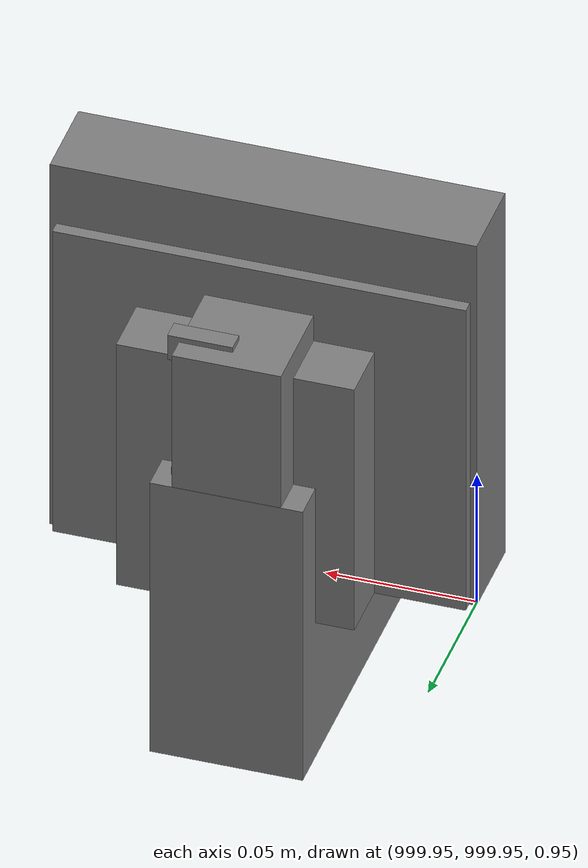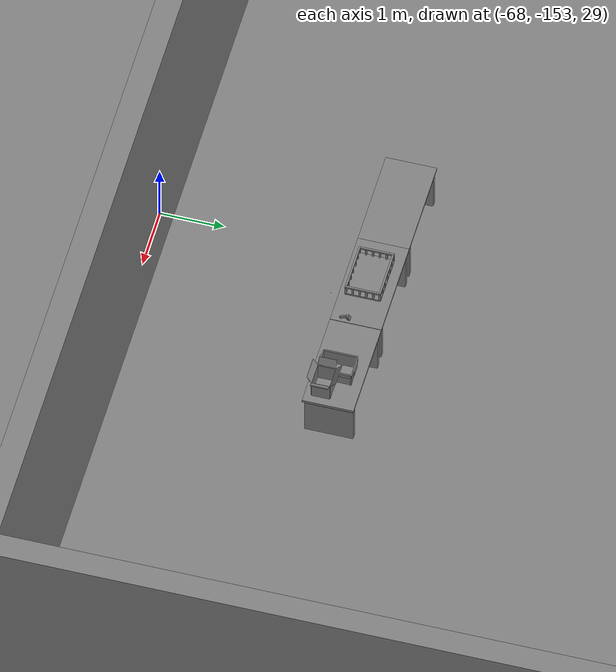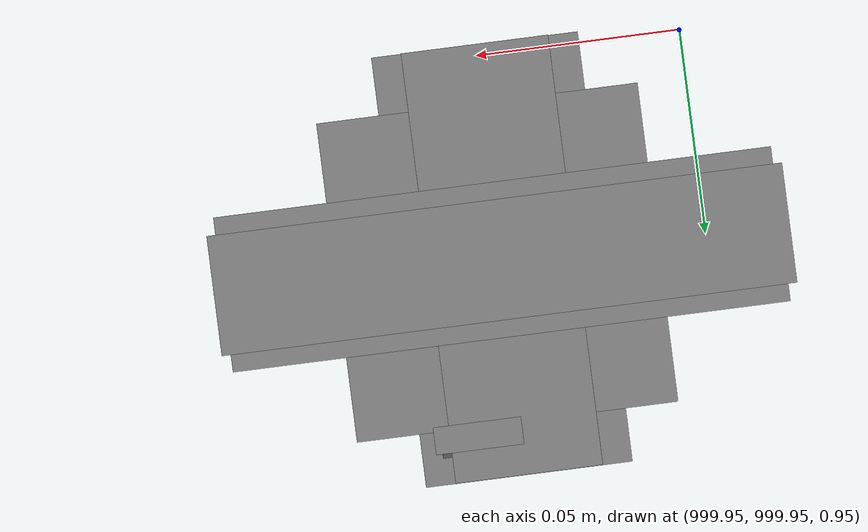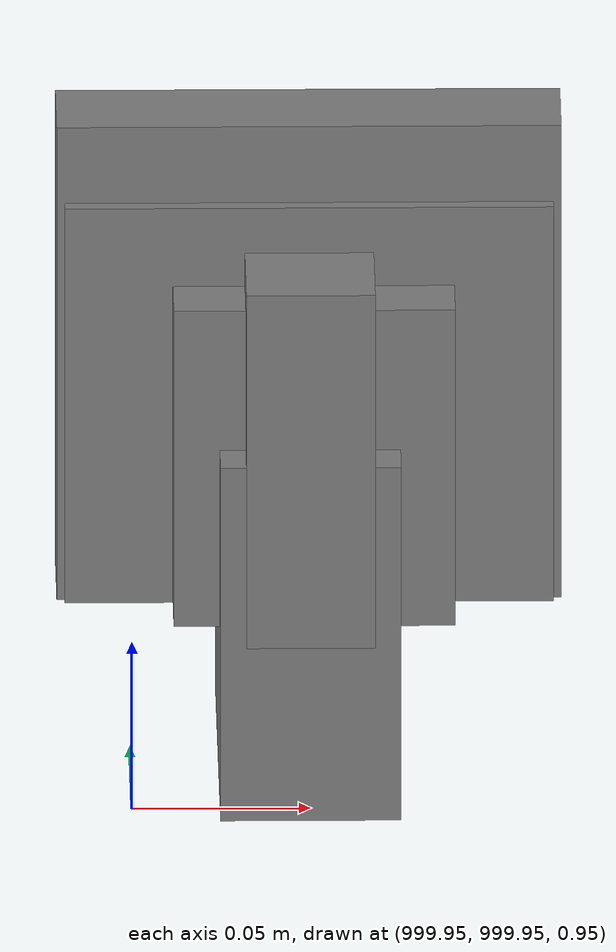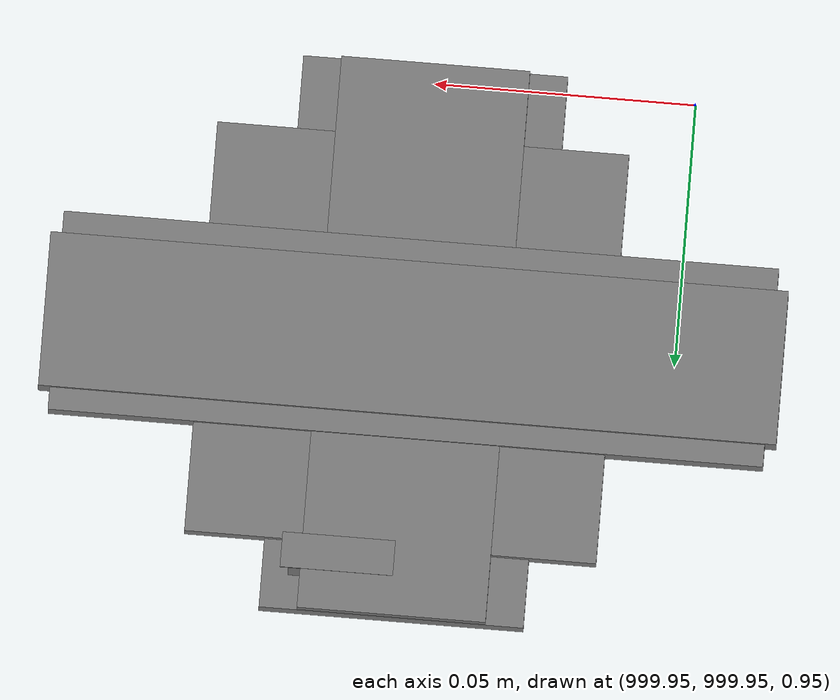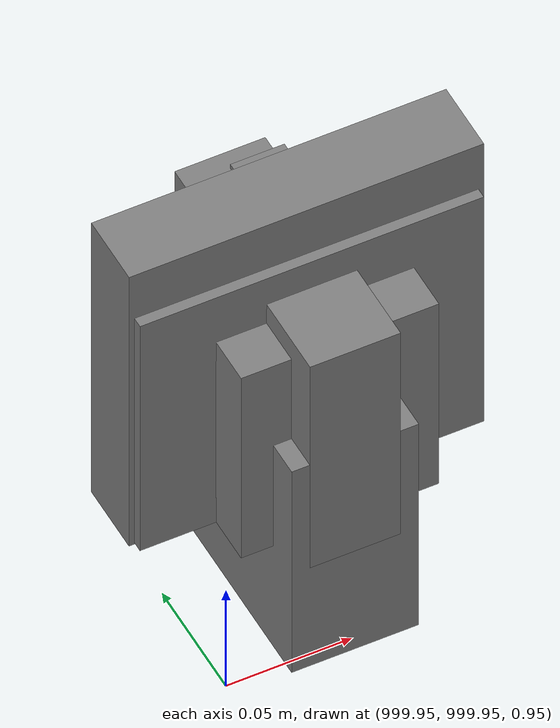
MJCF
<mujoco>
    <option gravity="0.000000000 0.000000000 -9.810000420" timestep="0.0049999999" integrator="implicitfast" density="1.225" viscosity="1.8000001e-05" noslip_iterations="10" iterations="100" sdf_iterations="50">
        <flag multiccd="disable"/>
    </option>
    <size memory="1000M"/>
    <compiler coordinate="local"/>
    <worldbody>
        <light cutoff="30" pos="0 1 1" dir="0 -1 -2"/>
        <light cutoff="30" pos="0 -1 1" dir="0 1 -2"/>
        <body pos="1000.000000000 1000.000000000 1.000000000" euler="0.000000000 0.000000000 180.000000000" name="openloong_gripper_2f85_fix_base_usda_cpu_fan">
            <geom contype="1" conaffinity="1" density="1000" type="box" material="" rgba="0.500000000 0.500000000 0.500000000 1.000000000" solimp="0.899999976 0.949999988 0.001000000" friction="1.000000000 0.005000000 0.000100000" solref="0.020000000 1.000000000" margin="0" condim="3" group="0" pos="0.000000000 0.000000000 0.070034981" quat="0.000000000 0.000000000 0.000000000 1.000000000" size="0.070700005 0.014699999 0.070700005" name="openloong_gripper_2f85_fix_base_usda_geom_5CBEF821_9C27_47D5_AF5A_7E4A1413D7BA"/>
            <freejoint name="openloong_gripper_2f85_fix_base_usda_cpu_fan_joint"/>
            <site size="0.005000000 0.005000000 0.005000000" rgba="0.500000000 0.500000000 0.500000000 1.000000000" pos="0.000000000 0.000000000 0.000000000" quat="0.999961913 0.008726535 0.000000000 0.000000000" group="0" type="sphere" name="openloong_gripper_2f85_fix_base_usda_cpu_fancsite"/>
        </body>
        <body pos="1000.000000000 1000.000000000 1.000000000" euler="0.000000000 0.000000000 180.000000000" name="openloong_gripper_2f85_fix_base_usda_battery_01">
            <geom contype="1" conaffinity="1" density="1000" type="box" material="" rgba="0.500000000 0.500000000 0.500000000 1.000000000" solimp="0.899999976 0.949999988 0.001000000" friction="1.000000000 0.005000000 0.000100000" solref="0.020000000 1.000000000" margin="0" condim="3" group="0" pos="-0.011123657 -0.041940309 0.101691343" quat="1.000000000 0.000000000 0.000000000 0.000000000" size="0.010800000 0.003375000 0.004725000" name="openloong_gripper_2f85_fix_base_usda_geom_D00A4504_DBDF_4406_B4E1_262D3919744E"/>
            <geom contype="1" conaffinity="1" density="1000" type="box" material="" rgba="0.500000000 0.500000000 0.500000000 1.000000000" solimp="0.899999976 0.949999988 0.001000000" friction="1.000000000 0.005000000 0.000100000" solref="0.020000000 1.000000000" margin="0" condim="3" group="0" pos="-0.010876465 -0.044247437 0.047066893" quat="0.998702705 -0.050920475 0.000000000 0.000000000" size="0.009450001 0.002700000 0.024975000" name="openloong_gripper_2f85_fix_base_usda_geom_BB525136_3CB9_42B5_B511_05E2DE85B0E1"/>
            <geom contype="1" conaffinity="1" density="1000" type="box" material="" rgba="0.500000000 0.500000000 0.500000000 1.000000000" solimp="0.899999976 0.949999988 0.001000000" friction="1.000000000 0.005000000 0.000100000" solref="0.020000000 1.000000000" margin="0" condim="3" group="0" pos="-0.001235962 -0.000659180 0.047381196" quat="1.000000000 0.000000000 0.000000000 0.000000000" size="0.039420001 0.039150000 0.047250003" name="openloong_gripper_2f85_fix_base_usda_geom_66301F5A_2890_48FE_96AC_29224AD85233"/>
            <geom contype="1" conaffinity="1" density="1000" type="box" material="" rgba="0.500000000 0.500000000 0.500000000 1.000000000" solimp="0.899999976 0.949999988 0.001000000" friction="1.000000000 0.005000000 0.000100000" solref="0.020000000 1.000000000" margin="0" condim="3" group="0" pos="-0.010876465 -0.039138794 0.009851727" quat="1.000000000 0.000000000 0.000000000 0.000000000" size="0.009450001 0.010800000 0.013500000" name="openloong_gripper_2f85_fix_base_usda_geom_CEE6080A_E451_4260_8479_D37E85759D7E"/>
            <geom contype="1" conaffinity="1" density="1000" type="box" material="" rgba="0.500000000 0.500000000 0.500000000 1.000000000" solimp="0.899999976 0.949999988 0.001000000" friction="1.000000000 0.005000000 0.000100000" solref="0.020000000 1.000000000" margin="0" condim="3" group="0" pos="-0.010876465 -0.041528322 0.071508206" quat="1.000000000 0.000000000 0.000000000 0.000000000" size="0.009450001 0.002700000 0.027000001" name="openloong_gripper_2f85_fix_base_usda_geom_9A2C995D_8AEF_4138_87A3_BD70E721D3B5"/>
            <freejoint name="openloong_gripper_2f85_fix_base_usda_battery_01_joint"/>
            <site size="0.005000000 0.005000000 0.005000000" rgba="0.500000000 0.500000000 0.500000000 1.000000000" pos="0.000000000 0.000000000 0.000000000" quat="0.999961913 0.008726500 0.000000000 0.000000000" group="0" type="sphere" name="openloong_gripper_2f85_fix_base_usda_battery_01site"/>
        </body>
        <body pos="-66.289230347 -149.627075195 31.166498184" euler="157.562927246 72.408020020 -132.082214355" mocap="true" name="spotlight3_SpotLight"/>
        <body pos="1000.000000000 1000.000000000 1.000000000" euler="0.000000000 0.000000000 180.000000000" name="openloong_gripper_2f85_fix_base_usda_wifi_box">
            <geom contype="1" conaffinity="1" density="1000" type="box" material="" rgba="0.500000000 0.500000000 0.500000000 1.000000000" solimp="0.899999976 0.949999988 0.001000000" friction="1.000000000 0.005000000 0.000100000" solref="0.020000000 1.000000000" margin="0" condim="3" group="0" pos="0.000000000 0.000000000 0.058978677" quat="0.000000000 0.000000047 0.000000000 1.000000000" size="0.068499997 0.018999999 0.059000000" name="openloong_gripper_2f85_fix_base_usda_geom_1735301E_4EAF_4160_BA1C_92D329A8AC77"/>
            <freejoint name="openloong_gripper_2f85_fix_base_usda_wifi_box_joint"/>
            <site size="0.005000000 0.005000000 0.005000000" rgba="0.500000000 0.500000000 0.500000000 1.000000000" pos="0.000000000 0.000000000 0.000000000" quat="0.999961913 0.008726500 0.000000000 0.000000000" group="0" type="sphere" name="openloong_gripper_2f85_fix_base_usda_wifi_boxsite"/>
        </body>
        <body pos="1000.000000000 1000.000000000 1.000000000" euler="0.000011953 0.000005123 -179.999984741" name="openloong_gripper_2f85_fix_base_usda_intel_box">
            <geom contype="1" conaffinity="1" density="1000" type="box" material="" rgba="0.500000000 0.500000000 0.500000000 1.000000000" solimp="0.899999976 0.949999988 0.001000000" friction="1.000000000 0.005000000 0.000100000" solref="0.020000000 1.000000000" margin="0" condim="3" group="0" pos="0.000000000 -0.000067139 0.000082284" quat="0.707106709 0.000000225 0.000000253 0.707106650" size="0.052800003 0.025300000 0.052800003" name="openloong_gripper_2f85_fix_base_usda_geom_197B65AF_EA02_4998_AF7F_22470FB27B17"/>
            <freejoint name="openloong_gripper_2f85_fix_base_usda_intel_box_joint"/>
            <site size="0.005000000 0.005000000 0.005000000" rgba="0.500000000 0.500000000 0.500000000 1.000000000" pos="0.000000000 0.000000000 0.000000000" quat="0.999961913 0.008726500 0.000000000 0.000000000" group="0" type="sphere" name="openloong_gripper_2f85_fix_base_usda_intel_boxsite"/>
        </body>
        <body pos="1000.000000000 999.999938965 1.000000000" euler="0.000000000 0.000000000 180.000000000" name="openloong_gripper_2f85_fix_base_usda_intelcore_i5">
            <geom contype="1" conaffinity="1" density="1000" type="box" material="" rgba="0.500000000 0.500000000 0.500000000 1.000000000" solimp="0.899999976 0.949999988 0.001000000" friction="1.000000000 0.005000000 0.000100000" solref="0.020000000 1.000000000" margin="0" condim="3" group="0" pos="0.000000000 0.000000000 0.051722717" quat="0.707106709 0.000000000 0.000000000 -0.707106769" size="0.052800000 0.018080002 0.052800000" name="openloong_gripper_2f85_fix_base_usda_geom_03BBA63E_FCC3_4A2D_90F0_A7DDEE25E234"/>
            <freejoint name="openloong_gripper_2f85_fix_base_usda_intelcore_i5_joint"/>
            <site size="0.005000000 0.005000000 0.005000000" rgba="0.500000000 0.500000000 0.500000000 1.000000000" pos="0.000000000 0.000000000 0.000000000" quat="0.999961913 0.008726534 0.000000000 0.000000000" group="0" type="sphere" name="openloong_gripper_2f85_fix_base_usda_intelcore_i5site"/>
        </body>
        <body pos="-66.394882202 -149.342178345 31.162704468" euler="39.029163361 -83.350074768 172.403747559" mocap="true" name="spotlight2_SpotLight"/>
        <body pos="-66.090736389 -149.203002930 31.166595459" euler="84.573722839 61.888149261 29.045429230" mocap="true" name="spotlight4_SpotLight"/>
        <body pos="-64.866622925 -149.383972168 30.183746338" euler="89.999984741 89.999946594 0.000000000" name="openloong_gripper_2f85_fix_base_usda_bluebox_01">
            <geom contype="1" conaffinity="1" density="1000" type="box" material="" rgba="0.500000000 0.500000000 0.500000000 1.000000000" solimp="0.899999976 0.949999988 0.001000000" friction="1.000000000 0.005000000 0.000100000" solref="0.020000000 1.000000000" margin="0" condim="3" group="0" pos="0.276580811 0.187225342 0.000068665" quat="0.707106948 0.000077471 0.707106352 0.000077486" size="0.100000001 0.057999998 0.010000000" name="openloong_gripper_2f85_fix_base_usda_geom_6A2DBACE_A1F7_40D2_87E6_F13E028E01B5"/>
            <geom contype="1" conaffinity="1" density="1000" type="box" material="" rgba="0.500000000 0.500000000 0.500000000 1.000000000" solimp="0.899999976 0.949999988 0.001000000" friction="1.000000000 0.005000000 0.000100000" solref="0.020000000 1.000000000" margin="0" condim="3" group="0" pos="0.000000000 0.002883911 0.000000000" quat="0.999999881 0.000000000 0.000000000 0.000000000" size="0.254000008 0.003000000 0.172000006" name="openloong_gripper_2f85_fix_base_usda_geom_BCEDD223_9BF1_4EF4_8D4B_1D4137043F93"/>
            <geom contype="1" conaffinity="1" density="1000" type="box" material="" rgba="0.500000000 0.500000000 0.500000000 1.000000000" solimp="0.899999976 0.949999988 0.001000000" friction="1.000000000 0.005000000 0.000100000" solref="0.020000000 1.000000000" margin="0" condim="3" group="0" pos="0.000000000 0.124874115 0.173484802" quat="0.999796331 0.020176515 -0.000000015 0.000000030" size="0.259999990 0.119999997 0.007000000" name="openloong_gripper_2f85_fix_base_usda_geom_0C0B01FA_C47E_4F36_B562_E12222E9BC91"/>
            <geom contype="1" conaffinity="1" density="1000" type="box" material="" rgba="0.500000000 0.500000000 0.500000000 1.000000000" solimp="0.899999976 0.949999988 0.001000000" friction="1.000000000 0.005000000 0.000100000" solref="0.020000000 1.000000000" margin="0" condim="3" group="0" pos="0.000000000 0.124874115 -0.173469543" quat="0.999796331 -0.020176545 -0.000000015 0.000000000" size="0.259999990 0.119999997 0.007000000" name="openloong_gripper_2f85_fix_base_usda_geom_2A0E9140_301B_4097_A72B_7BF20CF0EE47"/>
            <geom contype="1" conaffinity="1" density="1000" type="box" material="" rgba="0.500000000 0.500000000 0.500000000 1.000000000" solimp="0.899999976 0.949999988 0.001000000" friction="1.000000000 0.005000000 0.000100000" solref="0.020000000 1.000000000" margin="0" condim="3" group="0" pos="0.000000000 0.214008331 0.188980103" quat="0.999912977 0.013176724 0.000000015 0.000000000" size="0.259999990 0.029999999 0.012500000" name="openloong_gripper_2f85_fix_base_usda_geom_D034C8F4_854A_4512_99E0_20054CE5E696"/>
            <geom contype="1" conaffinity="1" density="1000" type="box" material="" rgba="0.500000000 0.500000000 0.500000000 1.000000000" solimp="0.899999976 0.949999988 0.001000000" friction="1.000000000 0.005000000 0.000100000" solref="0.020000000 1.000000000" margin="0" condim="3" group="0" pos="-0.258361816 0.125289917 0.001876831" quat="0.702796936 -0.020792112 0.710783124 0.020769298" size="0.189999998 0.119999997 0.009000000" name="openloong_gripper_2f85_fix_base_usda_geom_327B0B7F_1B88_49EC_9B44_6967342B1B27"/>
            <geom contype="1" conaffinity="1" density="1000" type="box" material="" rgba="0.500000000 0.500000000 0.500000000 1.000000000" solimp="0.899999976 0.949999988 0.001000000" friction="1.000000000 0.005000000 0.000100000" solref="0.020000000 1.000000000" margin="0" condim="3" group="0" pos="0.000000000 0.214008331 -0.188980103" quat="0.999912977 -0.013176769 0.000000030 0.000000015" size="0.259999990 0.029999999 0.012500000" name="openloong_gripper_2f85_fix_base_usda_geom_52F20C56_E239_4201_BAC5_919E722B7D7D"/>
            <geom contype="1" conaffinity="1" density="1000" type="box" material="" rgba="0.500000000 0.500000000 0.500000000 1.000000000" solimp="0.899999976 0.949999988 0.001000000" friction="1.000000000 0.005000000 0.000100000" solref="0.020000000 1.000000000" margin="0" condim="3" group="0" pos="-0.276611328 0.187225342 0.000068665" quat="0.707106650 0.000077441 0.707106709 0.000077456" size="0.100000001 0.057999998 0.010000000" name="openloong_gripper_2f85_fix_base_usda_geom_7F9AF616_CF3B_4486_8DD1_EAD96CC95055"/>
            <geom contype="1" conaffinity="1" density="1000" type="box" material="" rgba="0.500000000 0.500000000 0.500000000 1.000000000" solimp="0.899999976 0.949999988 0.001000000" friction="1.000000000 0.005000000 0.000100000" solref="0.020000000 1.000000000" margin="0" condim="3" group="0" pos="0.258331299 0.125289917 0.001876831" quat="0.702851415 0.018856421 0.710823774 -0.019329369" size="0.189999998 0.119999997 0.009000000" name="openloong_gripper_2f85_fix_base_usda_geom_AC03D988_C635_4E8F_8284_0AFE8D829E9C"/>
            <freejoint name="openloong_gripper_2f85_fix_base_usda_bluebox_01_joint"/>
            <site size="0.005000000 0.005000000 0.005000000" rgba="0.500000000 0.500000000 0.500000000 1.000000000" pos="0.000000000 0.000000000 0.000000000" quat="0.999961913 0.008726534 0.000000000 0.000000000" group="0" type="sphere" name="openloong_gripper_2f85_fix_base_usda_bluebox_01site"/>
        </body>
        <body pos="-64.496299744 -149.491867065 30.235729218" euler="0.000000000 0.000000000 89.999946594" name="openloong_gripper_2f85_fix_base_usda_cardboardbox_01">
            <geom contype="1" conaffinity="1" density="1000" type="box" material="" rgba="0.500000000 0.500000000 0.500000000 1.000000000" solimp="0.899999976 0.949999988 0.001000000" friction="1.000000000 0.005000000 0.000100000" solref="0.020000000 1.000000000" margin="0" condim="3" group="0" pos="-0.003166199 -0.004086494 0.005052090" quat="1.000000000 0.000000000 0.000000000 0.000000000" size="0.142499998 0.177500010 0.005000000" name="openloong_gripper_2f85_fix_base_usda_geom_916E83B8_B407_4550_90A2_1FA70B178BB3"/>
            <geom contype="1" conaffinity="1" density="1000" type="box" material="" rgba="0.500000000 0.500000000 0.500000000 1.000000000" solimp="0.899999976 0.949999988 0.001000000" friction="1.000000000 0.005000000 0.000100000" solref="0.020000000 1.000000000" margin="0" condim="3" group="0" pos="-0.003166199 0.170316696 0.150570869" quat="1.000000000 0.000000000 0.000000000 0.000000000" size="0.142499998 0.005000000 0.149999991" name="openloong_gripper_2f85_fix_base_usda_geom_A323F8CF_1F54_4CEB_942C_DB9E0469B9C0"/>
            <geom contype="1" conaffinity="1" density="1000" type="box" material="" rgba="0.500000000 0.500000000 0.500000000 1.000000000" solimp="0.899999976 0.949999988 0.001000000" friction="1.000000000 0.005000000 0.000100000" solref="0.020000000 1.000000000" margin="0" condim="3" group="0" pos="-0.147399902 -0.005307198 0.150570869" quat="1.000000000 0.000000000 0.000000000 0.000000000" size="0.005000000 0.177500010 0.149999991" name="openloong_gripper_2f85_fix_base_usda_geom_C9FD67BB_A667_40A4_B9EC_1C544B641874"/>
            <geom contype="1" conaffinity="1" density="1000" type="box" material="" rgba="0.500000000 0.500000000 0.500000000 1.000000000" solimp="0.899999976 0.949999988 0.001000000" friction="1.000000000 0.005000000 0.000100000" solref="0.020000000 1.000000000" margin="0" condim="3" group="0" pos="0.140275955 -0.005307198 0.150570869" quat="1.000000000 0.000000000 0.000000000 0.000000000" size="0.005000000 0.177500010 0.149999991" name="openloong_gripper_2f85_fix_base_usda_geom_C43931AD_6045_409E_8453_F1AA630D4AF4"/>
            <geom contype="1" conaffinity="1" density="1000" type="box" material="" rgba="0.500000000 0.500000000 0.500000000 1.000000000" solimp="0.899999976 0.949999988 0.001000000" friction="1.000000000 0.005000000 0.000100000" solref="0.020000000 1.000000000" margin="0" condim="3" group="0" pos="-0.003166199 -0.181550980 0.150570869" quat="1.000000000 0.000000000 0.000000000 0.000000000" size="0.142499998 0.005000000 0.149999991" name="openloong_gripper_2f85_fix_base_usda_geom_CD4F3D5E_DD33_4A28_A692_606F2A4E5D04"/>
            <freejoint name="openloong_gripper_2f85_fix_base_usda_cardboardbox_01_joint"/>
            <site size="0.005000000 0.005000000 0.005000000" rgba="0.500000000 0.500000000 0.500000000 1.000000000" pos="0.000000000 0.000000000 0.000000000" quat="0.999961913 0.008726535 0.000000000 0.000000000" group="0" type="sphere" name="openloong_gripper_2f85_fix_base_usda_site_BA3BB7CB_0523_4FCF_B29C_22169036C8E7"/>
            <body pos="0.139160156 -0.004048347 0.301930904" euler="-179.999954224 49.383502960 179.999954224" name="openloong_gripper_2f85_fix_base_usda_A1_006">
                <geom contype="1" conaffinity="1" density="1000" type="box" material="" rgba="0.500000000 0.500000000 0.500000000 1.000000000" solimp="0.899999976 0.949999988 0.001000000" friction="1.000000000 0.005000000 0.000100000" solref="0.020000000 1.000000000" margin="0" condim="3" group="0" pos="-0.071587563 0.000009537 0.001745224" quat="0.999999881 0.000000000 0.000000000 0.000000000" size="0.071249999 0.179999992 0.002500000" name="openloong_gripper_2f85_fix_base_usda_geom_74AF6425_7D4C_4311_A3C1_D4D52DCBE7E7"/>
                <joint armature="0" stiffness="0.07" damping="0.0099999998" axis="0.000000 1.000000 0.000000" type="hinge" name="openloong_gripper_2f85_fix_base_usda_A1_006"/>
            </body>
            <body pos="-0.145902634 -0.004086494 0.301938057" euler="-180.000000000 -60.000011444 -180.000000000" name="openloong_gripper_2f85_fix_base_usda_A2_006">
                <geom contype="1" conaffinity="1" density="1000" type="box" material="" rgba="0.500000000 0.500000000 0.500000000 1.000000000" solimp="0.899999976 0.949999988 0.001000000" friction="1.000000000 0.005000000 0.000100000" solref="0.020000000 1.000000000" margin="0" condim="3" group="0" pos="0.071268082 0.000009537 0.002717972" quat="0.000002921 0.000000000 -0.000000030 0.999999881" size="0.071249999 0.179999992 0.002500000" name="openloong_gripper_2f85_fix_base_usda_geom_5D2A59B5_3268_484A_A56D_1191752C8576"/>
                <joint armature="0" stiffness="0.07" damping="0.0099999998" axis="0.000000 1.000000 0.000000" type="hinge" name="openloong_gripper_2f85_fix_base_usda_A2_006"/>
            </body>
            <body pos="-0.003385544 0.175991058 0.301930904" euler="-125.858116150 -0.000004561 0.000002331" name="openloong_gripper_2f85_fix_base_usda_B2_006">
                <geom contype="1" conaffinity="1" density="1000" type="box" material="" rgba="0.500000000 0.500000000 0.500000000 1.000000000" solimp="0.899999976 0.949999988 0.001000000" friction="1.000000000 0.005000000 0.000100000" solref="0.020000000 1.000000000" margin="0" condim="3" group="0" pos="0.000009537 -0.070939064 -0.002470016" quat="0.999614120 0.027776197 -0.000000015 0.000000030" size="0.137500003 0.064999998 0.005000000" name="openloong_gripper_2f85_fix_base_usda_geom_52CB3148_3475_417F_B9D1_F42BB9590CB9"/>
                <joint armature="0" stiffness="0.07" damping="0.0099999998" axis="1.000000 0.000000 0.000000" type="hinge" name="openloong_gripper_2f85_fix_base_usda_B2_006"/>
            </body>
            <body pos="-0.003385544 -0.184140205 0.301938057" euler="147.805557251 0.000000000 0.000000000" name="openloong_gripper_2f85_fix_base_usda_B1_006">
                <geom contype="1" conaffinity="1" density="1000" type="box" material="" rgba="0.500000000 0.500000000 0.500000000 1.000000000" solimp="0.899999976 0.949999988 0.001000000" friction="1.000000000 0.005000000 0.000100000" solref="0.020000000 1.000000000" margin="0" condim="3" group="0" pos="-0.000028610 0.070202351 -0.002703667" quat="0.999614179 -0.027776167 0.000000000 0.000000000" size="0.137500003 0.064999998 0.005000000" name="openloong_gripper_2f85_fix_base_usda_geom_86731B33_F043_476F_B7B4_A5D6F8399808"/>
                <joint armature="0" stiffness="0.07" damping="0.0099999998" axis="1.000000 0.000000 0.000000" type="hinge" name="openloong_gripper_2f85_fix_base_usda_B1_006"/>
            </body>
        </body>
        <body pos="-65.882858276 -149.481979370 30.229999542" euler="-64.487716675 0.000000000 0.000000000" name="openloong_gripper_2f85_fix_base_usda_Barcode">
            <geom contype="1" conaffinity="1" density="1000" type="box" material="" rgba="0.500000000 0.500000000 0.500000000 1.000000000" solimp="0.899999976 0.949999988 0.001000000" friction="1.000000000 0.005000000 0.000100000" solref="0.020000000 1.000000000" margin="0" condim="3" group="0" pos="0.000000000 0.013038635 0.001419067" quat="0.000000000 0.000000000 0.000000000 1.000000119" size="0.034000002 0.010000000 0.017999999" name="openloong_gripper_2f85_fix_base_usda_geom_C6ACACCD_7A27_4D26_8333_2B90FEF86CA5"/>
            <geom contype="1" conaffinity="1" density="1000" type="box" material="" rgba="0.500000000 0.500000000 0.500000000 1.000000000" solimp="0.899999976 0.949999988 0.001000000" friction="1.000000000 0.005000000 0.000100000" solref="0.020000000 1.000000000" margin="0" condim="3" group="0" pos="0.000000000 -0.035301208 -0.007095337" quat="0.000000000 0.000000000 -0.043619365 0.999048233" size="0.028999999 0.010000000 0.020000000" name="openloong_gripper_2f85_fix_base_usda_geom_C5A3F5DF_5C17_41D9_8CFB_AE026FCC772F"/>
            <geom contype="1" conaffinity="1" density="1000" type="box" material="" rgba="0.500000000 0.500000000 0.500000000 1.000000000" solimp="0.899999976 0.949999988 0.001000000" friction="1.000000000 0.005000000 0.000100000" solref="0.020000000 1.000000000" margin="0" condim="3" group="0" pos="0.000000000 -0.043411255 -0.011749268" quat="0.922262907 0.386563420 0.000000000 0.000000000" size="0.026000001 0.010000000 0.020000000" name="openloong_gripper_2f85_fix_base_usda_geom_03CE0759_3ECC_40E8_978D_B6B61AFF1899"/>
            <geom contype="1" conaffinity="1" density="1000" type="box" material="" rgba="0.500000000 0.500000000 0.500000000 1.000000000" solimp="0.899999976 0.949999988 0.001000000" friction="1.000000000 0.005000000 0.000100000" solref="0.020000000 1.000000000" margin="0" condim="3" group="0" pos="0.000000000 -0.016967773 -0.031860352" quat="0.000000000 0.000000000 0.000000000 1.000000119" size="0.008000000 0.010000000 0.013000000" name="openloong_gripper_2f85_fix_base_usda_geom_9617F4DD_5314_492B_9327_4210D8D291E4"/>
            <geom contype="1" conaffinity="1" density="1000" type="box" material="" rgba="0.500000000 0.500000000 0.500000000 1.000000000" solimp="0.899999976 0.949999988 0.001000000" friction="1.000000000 0.005000000 0.000100000" solref="0.020000000 1.000000000" margin="0" condim="3" group="0" pos="0.000000000 -0.001869202 0.000312805" quat="0.953716993 0.300705761 0.000000000 0.000000000" size="0.032000002 0.010000000 0.018999999" name="openloong_gripper_2f85_fix_base_usda_geom_28120BF1_B827_4452_9407_0C0030B917A2"/>
            <geom contype="1" conaffinity="1" density="1000" type="box" material="" rgba="0.500000000 0.500000000 0.500000000 1.000000000" solimp="0.899999976 0.949999988 0.001000000" friction="1.000000000 0.005000000 0.000100000" solref="0.020000000 1.000000000" margin="0" condim="3" group="0" pos="0.000000000 -0.019531250 -0.003173828" quat="0.953716993 0.300705761 0.000000000 0.000000000" size="0.030999999 0.010000000 0.020000000" name="openloong_gripper_2f85_fix_base_usda_geom_DE9AA07D_C84F_497C_9685_9FC6457D9B78"/>
            <geom contype="1" conaffinity="1" density="1000" type="box" material="" rgba="0.500000000 0.500000000 0.500000000 1.000000000" solimp="0.899999976 0.949999988 0.001000000" friction="1.000000000 0.005000000 0.000100000" solref="0.020000000 1.000000000" margin="0" condim="3" group="0" pos="0.000000000 -0.035301208 -0.007095337" quat="0.953716993 0.300705761 0.000000000 0.000000000" size="0.028999999 0.010000000 0.020000000" name="openloong_gripper_2f85_fix_base_usda_geom_76DB4735_B827_40B6_AFB8_D37D3CFFC963"/>
            <geom contype="1" conaffinity="1" density="1000" type="box" material="" rgba="0.500000000 0.500000000 0.500000000 1.000000000" solimp="0.899999976 0.949999988 0.001000000" friction="1.000000000 0.005000000 0.000100000" solref="0.020000000 1.000000000" margin="0" condim="3" group="0" pos="0.000000000 -0.042617798 -0.071121216" quat="0.000000000 0.000000000 0.000000000 1.000000119" size="0.013000000 0.021000000 0.059999999" name="openloong_gripper_2f85_fix_base_usda_geom_A4739674_C3F2_4901_AAA9_1F4F722D2318"/>
            <freejoint name="openloong_gripper_2f85_fix_base_usda_Barcode_joint"/>
            <site size="0.005000000 0.005000000 0.005000000" rgba="0.500000000 0.500000000 0.500000000 1.000000000" pos="0.000000000 0.000000000 0.000000000" quat="1.000000000 0.000000000 0.000000000 0.000000000" group="0" type="sphere" name="openloong_gripper_2f85_fix_base_usda_Barcode_site"/>
        </body>
        <body pos="-66.745018005 -149.392349243 30.184000015" euler="0.000000000 0.000000000 89.999946594" name="[22330699446220]_Basket_01">
            <geom contype="1" conaffinity="1" density="1000" type="box" material="" rgba="0.500000000 0.500000000 0.500000000 1.000000000" solimp="0.899999976 0.949999988 0.001000000" friction="1.000000000 0.005000000 0.000100000" solref="0.020000000 1.000000000" margin="0" condim="3" group="0" pos="-0.052425385 0.389207840 0.089787483" quat="0.707107008 0.000000000 0.000000000 0.707106411" size="0.014249999 0.014249999 0.059999999" name="[22330699446220]_geom_B899296D_C208_4413_9610_0BD26D85AF94"/>
            <geom contype="1" conaffinity="1" density="1000" type="box" material="" rgba="0.500000000 0.500000000 0.500000000 1.000000000" solimp="0.899999976 0.949999988 0.001000000" friction="1.000000000 0.005000000 0.000100000" solref="0.020000000 1.000000000" margin="0" condim="3" group="0" pos="0.264015198 -0.133043289 0.089787483" quat="0.707107008 0.000000000 0.000000000 0.707106411" size="0.014249999 0.014249999 0.059999999" name="[22330699446220]_geom_4ADF4565_AEFE_4094_A53B_A2E0CA4743D1"/>
            <geom contype="1" conaffinity="1" density="1000" type="box" material="" rgba="0.500000000 0.500000000 0.500000000 1.000000000" solimp="0.899999976 0.949999988 0.001000000" friction="1.000000000 0.005000000 0.000100000" solref="0.020000000 1.000000000" margin="0" condim="3" group="0" pos="-0.264015198 -0.265548706 0.089793205" quat="0.707107008 0.000000000 0.000000000 0.707106411" size="0.014249999 0.014249999 0.059999999" name="[22330699446220]_geom_ABA3C0F9_12C8_431F_943E_4B64214C5C9B"/>
            <geom contype="1" conaffinity="1" density="1000" type="box" material="" rgba="0.500000000 0.500000000 0.500000000 1.000000000" solimp="0.899999976 0.949999988 0.001000000" friction="1.000000000 0.005000000 0.000100000" solref="0.020000000 1.000000000" margin="0" condim="3" group="0" pos="-0.160263062 -0.389322281 0.089793205" quat="0.707107008 0.000000000 0.000000000 0.707106411" size="0.014249999 0.014249999 0.059999999" name="[22330699446220]_geom_7F6CB983_1710_4980_86F6_F6B15A6B3B25"/>
            <geom contype="1" conaffinity="1" density="1000" type="box" material="" rgba="0.500000000 0.500000000 0.500000000 1.000000000" solimp="0.899999976 0.949999988 0.001000000" friction="1.000000000 0.005000000 0.000100000" solref="0.020000000 1.000000000" margin="0" condim="3" group="0" pos="0.162265778 -0.389322281 0.089787483" quat="0.707107008 0.000000000 0.000000000 0.707106411" size="0.014249999 0.014249999 0.059999999" name="[22330699446220]_geom_BCD3C5FA_6A48_45DC_B086_6A95194C73B9"/>
            <geom contype="1" conaffinity="1" density="1000" type="box" material="" rgba="0.500000000 0.500000000 0.500000000 1.000000000" solimp="0.899999976 0.949999988 0.001000000" friction="1.000000000 0.005000000 0.000100000" solref="0.020000000 1.000000000" margin="0" condim="3" group="0" pos="0.264015198 0.389207840 0.089787483" quat="0.707107008 0.000000000 0.000000000 0.707106411" size="0.014249999 0.014249999 0.059999999" name="[22330699446220]_geom_A95366B5_D1CC_4011_A040_BB151C2FD2E7"/>
            <geom contype="1" conaffinity="1" density="1000" type="box" material="" rgba="0.500000000 0.500000000 0.500000000 1.000000000" solimp="0.899999976 0.949999988 0.001000000" friction="1.000000000 0.005000000 0.000100000" solref="0.020000000 1.000000000" margin="0" condim="3" group="0" pos="-0.264015198 -0.133043289 0.089793205" quat="0.707107008 0.000000000 0.000000000 0.707106411" size="0.014249999 0.014249999 0.059999999" name="[22330699446220]_geom_22A3A40C_DBB6_498B_AD22_455A860FEE2B"/>
            <geom contype="1" conaffinity="1" density="1000" type="box" material="" rgba="0.500000000 0.500000000 0.500000000 1.000000000" solimp="0.899999976 0.949999988 0.001000000" friction="1.000000000 0.005000000 0.000100000" solref="0.020000000 1.000000000" margin="0" condim="3" group="0" pos="-0.264026642 0.269256592 0.089793205" quat="0.707107008 0.000000000 0.000000000 0.707106411" size="0.014249999 0.014249999 0.059999999" name="[22330699446220]_geom_0CFA7464_A7A8_4768_8D4E_1DD201E88013"/>
            <geom contype="1" conaffinity="1" density="1000" type="box" material="" rgba="0.500000000 0.500000000 0.500000000 1.000000000" solimp="0.899999976 0.949999988 0.001000000" friction="1.000000000 0.005000000 0.000100000" solref="0.020000000 1.000000000" margin="0" condim="3" group="0" pos="0.054462433 0.389207840 0.089787483" quat="0.707107008 0.000000000 0.000000000 0.707106411" size="0.014249999 0.014249999 0.059999999" name="[22330699446220]_geom_7043F2AC_8A01_4DD5_AAE5_CA248C7C2B4E"/>
            <geom contype="1" conaffinity="1" density="1000" type="box" material="" rgba="0.500000000 0.500000000 0.500000000 1.000000000" solimp="0.899999976 0.949999988 0.001000000" friction="1.000000000 0.005000000 0.000100000" solref="0.020000000 1.000000000" margin="0" condim="3" group="0" pos="0.054462433 -0.389322281 0.089787483" quat="0.707107008 0.000000000 0.000000000 0.707106411" size="0.014249999 0.014249999 0.059999999" name="[22330699446220]_geom_D696A056_0CDC_4614_BA11_95562B59FE7C"/>
            <geom contype="1" conaffinity="1" density="1000" type="box" material="" rgba="0.500000000 0.500000000 0.500000000 1.000000000" solimp="0.899999976 0.949999988 0.001000000" friction="1.000000000 0.005000000 0.000100000" solref="0.020000000 1.000000000" margin="0" condim="3" group="0" pos="0.264015198 0.269256592 0.089793205" quat="0.707107008 0.000000000 0.000000000 0.707106411" size="0.014249999 0.014249999 0.059999999" name="[22330699446220]_geom_FE18897F_C0BB_4EAF_BAB7_5C927FA77459"/>
            <geom contype="1" conaffinity="1" density="1000" type="box" material="" rgba="0.500000000 0.500000000 0.500000000 1.000000000" solimp="0.899999976 0.949999988 0.001000000" friction="1.000000000 0.005000000 0.000100000" solref="0.020000000 1.000000000" margin="0" condim="3" group="0" pos="0.264015198 -0.389322281 0.089787483" quat="0.707107008 0.000000000 0.000000000 0.707106411" size="0.014249999 0.014249999 0.059999999" name="[22330699446220]_geom_E0F0F1EE_30BB_4559_B6EF_F2F003A11790"/>
            <geom contype="1" conaffinity="1" density="1000" type="box" material="" rgba="0.500000000 0.500000000 0.500000000 1.000000000" solimp="0.899999976 0.949999988 0.001000000" friction="1.000000000 0.005000000 0.000100000" solref="0.020000000 1.000000000" margin="0" condim="3" group="0" pos="0.000000000 0.000000000 0.015998840" quat="0.707107008 0.000000000 0.000000000 0.707106411" size="0.403499991 0.279000014 0.015750000" name="[22330699446220]_geom_70DE2036_4174_4BFC_9EF0_F427A64EEDA5"/>
            <geom contype="1" conaffinity="1" density="1000" type="box" material="" rgba="0.500000000 0.500000000 0.500000000 1.000000000" solimp="0.899999976 0.949999988 0.001000000" friction="1.000000000 0.005000000 0.000100000" solref="0.020000000 1.000000000" margin="0" condim="3" group="0" pos="0.000000000 -0.389476776 0.163619041" quat="0.707107008 0.000000000 0.000000000 0.707106411" size="0.015000000 0.277500004 0.015750000" name="[22330699446220]_geom_73283977_14A3_41A9_A95C_2017F9C1F30B"/>
            <geom contype="1" conaffinity="1" density="1000" type="box" material="" rgba="0.500000000 0.500000000 0.500000000 1.000000000" solimp="0.899999976 0.949999988 0.001000000" friction="1.000000000 0.005000000 0.000100000" solref="0.020000000 1.000000000" margin="0" condim="3" group="0" pos="0.162265778 0.389207840 0.089787483" quat="0.707107008 0.000000000 0.000000000 0.707106411" size="0.014249999 0.014249999 0.059999999" name="[22330699446220]_geom_3C4662B7_709D_4BA5_A396_8F1F746B4A12"/>
            <geom contype="1" conaffinity="1" density="1000" type="box" material="" rgba="0.500000000 0.500000000 0.500000000 1.000000000" solimp="0.899999976 0.949999988 0.001000000" friction="1.000000000 0.005000000 0.000100000" solref="0.020000000 1.000000000" margin="0" condim="3" group="0" pos="0.000000000 0.389471054 0.163619041" quat="0.707107008 0.000000000 0.000000000 0.707106411" size="0.015000000 0.277500004 0.015750000" name="[22330699446220]_geom_22DA8BC0_25FE_485A_9A25_C55CB695FA55"/>
            <geom contype="1" conaffinity="1" density="1000" type="box" material="" rgba="0.500000000 0.500000000 0.500000000 1.000000000" solimp="0.899999976 0.949999988 0.001000000" friction="1.000000000 0.005000000 0.000100000" solref="0.020000000 1.000000000" margin="0" condim="3" group="0" pos="-0.263511658 0.000000000 0.163619041" quat="0.707107008 0.000000000 0.000000000 0.707106411" size="0.403499991 0.015000000 0.015750000" name="[22330699446220]_geom_CDCC62F6_58E3_4E25_93CC_5059385C7D76"/>
            <geom contype="1" conaffinity="1" density="1000" type="box" material="" rgba="0.500000000 0.500000000 0.500000000 1.000000000" solimp="0.899999976 0.949999988 0.001000000" friction="1.000000000 0.005000000 0.000100000" solref="0.020000000 1.000000000" margin="0" condim="3" group="0" pos="-0.264015198 0.141334534 0.089793205" quat="0.707107008 0.000000000 0.000000000 0.707106411" size="0.014249999 0.014249999 0.059999999" name="[22330699446220]_geom_BA6D02F8_47AD_423B_AD95_7AAAFE269274"/>
            <geom contype="1" conaffinity="1" density="1000" type="box" material="" rgba="0.500000000 0.500000000 0.500000000 1.000000000" solimp="0.899999976 0.949999988 0.001000000" friction="1.000000000 0.005000000 0.000100000" solref="0.020000000 1.000000000" margin="0" condim="3" group="0" pos="0.264015198 -0.265548706 0.089787483" quat="0.707107008 0.000000000 0.000000000 0.707106411" size="0.014249999 0.014249999 0.059999999" name="[22330699446220]_geom_85512903_5791_4AAE_88C4_09DB54DF0B1B"/>
            <geom contype="1" conaffinity="1" density="1000" type="box" material="" rgba="0.500000000 0.500000000 0.500000000 1.000000000" solimp="0.899999976 0.949999988 0.001000000" friction="1.000000000 0.005000000 0.000100000" solref="0.020000000 1.000000000" margin="0" condim="3" group="0" pos="-0.160263062 0.389207840 0.089787483" quat="0.707107008 0.000000000 0.000000000 0.707106411" size="0.014249999 0.014249999 0.059999999" name="[22330699446220]_geom_63E782F5_36BF_4950_A39C_E54585E84337"/>
            <geom contype="1" conaffinity="1" density="1000" type="box" material="" rgba="0.500000000 0.500000000 0.500000000 1.000000000" solimp="0.899999976 0.949999988 0.001000000" friction="1.000000000 0.005000000 0.000100000" solref="0.020000000 1.000000000" margin="0" condim="3" group="0" pos="-0.052425385 -0.389322281 0.089787483" quat="0.707107008 0.000000000 0.000000000 0.707106411" size="0.014249999 0.014249999 0.059999999" name="[22330699446220]_geom_7F6A7322_5521_4B5C_BE44_7AF9CFFEA8ED"/>
            <geom contype="1" conaffinity="1" density="1000" type="box" material="" rgba="0.500000000 0.500000000 0.500000000 1.000000000" solimp="0.899999976 0.949999988 0.001000000" friction="1.000000000 0.005000000 0.000100000" solref="0.020000000 1.000000000" margin="0" condim="3" group="0" pos="-0.264026642 -0.389322281 0.089793205" quat="0.707107008 0.000000000 0.000000000 0.707106411" size="0.014249999 0.014249999 0.059999999" name="[22330699446220]_geom_4DE0A9E4_A0E1_4D3A_A219_BF2F42774F0D"/>
            <geom contype="1" conaffinity="1" density="1000" type="box" material="" rgba="0.500000000 0.500000000 0.500000000 1.000000000" solimp="0.899999976 0.949999988 0.001000000" friction="1.000000000 0.005000000 0.000100000" solref="0.020000000 1.000000000" margin="0" condim="3" group="0" pos="0.264015198 0.141334534 0.089787483" quat="0.707107008 0.000000000 0.000000000 0.707106411" size="0.014249999 0.014249999 0.059999999" name="[22330699446220]_geom_DE175232_270B_43BF_A7CA_3299C0D2E5F4"/>
            <geom contype="1" conaffinity="1" density="1000" type="box" material="" rgba="0.500000000 0.500000000 0.500000000 1.000000000" solimp="0.899999976 0.949999988 0.001000000" friction="1.000000000 0.005000000 0.000100000" solref="0.020000000 1.000000000" margin="0" condim="3" group="0" pos="-0.264015198 0.389207840 0.089793205" quat="0.707107008 0.000000000 0.000000000 0.707106411" size="0.014249999 0.014249999 0.059999999" name="[22330699446220]_geom_C64E0C02_6A90_44C8_8AC3_9AA1278C5D71"/>
            <geom contype="1" conaffinity="1" density="1000" type="box" material="" rgba="0.500000000 0.500000000 0.500000000 1.000000000" solimp="0.899999976 0.949999988 0.001000000" friction="1.000000000 0.005000000 0.000100000" solref="0.020000000 1.000000000" margin="0" condim="3" group="0" pos="0.264015198 0.004480362 0.089787483" quat="0.707107008 0.000000000 0.000000000 0.707106411" size="0.014249999 0.014249999 0.059999999" name="[22330699446220]_geom_7DBA0869_4A05_4D9F_B369_C5E45856BE3F"/>
            <geom contype="1" conaffinity="1" density="1000" type="box" material="" rgba="0.500000000 0.500000000 0.500000000 1.000000000" solimp="0.899999976 0.949999988 0.001000000" friction="1.000000000 0.005000000 0.000100000" solref="0.020000000 1.000000000" margin="0" condim="3" group="0" pos="0.263694763 -0.000011444 0.163619041" quat="0.707107008 0.000000000 0.000000000 0.707106411" size="0.403499991 0.015000000 0.015750000" name="[22330699446220]_geom_9421A604_4DE8_46BC_993C_6350B66F4029"/>
            <geom contype="1" conaffinity="1" density="1000" type="box" material="" rgba="0.500000000 0.500000000 0.500000000 1.000000000" solimp="0.899999976 0.949999988 0.001000000" friction="1.000000000 0.005000000 0.000100000" solref="0.020000000 1.000000000" margin="0" condim="3" group="0" pos="-0.264015198 0.004480362 0.089793205" quat="0.707107008 0.000000000 0.000000000 0.707106411" size="0.014249999 0.014249999 0.059999999" name="[22330699446220]_geom_A6AAFB8D_D8C9_4B9E_B68F_A23CEB60518A"/>
            <freejoint name="[22330699446220]_joint_5641B938_631E_4344_A96B_45F712E63627"/>
        </body>
        <body pos="0.000000000 0.000000000 0.000000000" euler="0.000000000 0.000000000 0.000000000" name="Static Objects_Static Objects">
            <geom contype="1" conaffinity="1" density="1000" type="box" material="" rgba="0.500000000 0.500000000 0.500000000 1.000000000" solimp="0.899999976 0.949999988 0.001000000" friction="1.000000000 0.005000000 0.000100000" solref="0.020000000 1.000000000" margin="0" condim="3" group="0" pos="-67.544113159 -149.365814209 29.727830887" quat="0.500000417 0.499999970 0.499999553 0.499999970" size="0.381000012 0.319999993 0.041000001" name="Static Objects_geom_6980153D_9124_4BBF_BCC7_DCE73A17F247"/>
            <geom contype="1" conaffinity="1" density="1000" type="box" material="" rgba="0.500000000 0.500000000 0.500000000 1.000000000" solimp="0.899999976 0.949999988 0.001000000" friction="1.000000000 0.005000000 0.000100000" solref="0.020000000 1.000000000" margin="0" condim="3" group="0" pos="-68.239501953 -149.365814209 30.086868286" quat="0.500000417 0.499999970 0.499999553 0.499999970" size="0.370999992 0.039500002 0.745000005" name="Static Objects_geom_FCEF26CB_0F9C_4D52_A7C7_B8FE0B21D6B7"/>
            <geom contype="1" conaffinity="1" density="1000" type="box" material="" rgba="0.500000000 0.500000000 0.500000000 1.000000000" solimp="0.899999976 0.949999988 0.001000000" friction="1.000000000 0.005000000 0.000100000" solref="0.020000000 1.000000000" margin="0" condim="3" group="0" pos="-68.239501953 -149.365814209 30.147235870" quat="0.500000417 0.499999970 0.499999553 0.499999970" size="0.400000006 0.022000000 0.800000012" name="Static Objects_geom_AEA908DF_8A50_4186_BEC6_353797FBABD1"/>
            <geom contype="1" conaffinity="1" density="1000" type="box" material="" rgba="0.500000000 0.500000000 0.500000000 1.000000000" solimp="0.899999976 0.949999988 0.001000000" friction="1.000000000 0.005000000 0.000100000" solref="0.020000000 1.000000000" margin="0" condim="3" group="0" pos="-68.934890747 -149.365814209 29.727830887" quat="0.500000417 0.499999970 0.499999553 0.499999970" size="0.381000012 0.319999993 0.041000001" name="Static Objects_geom_0C07A379_5C9A_4BB8_8F4E_8105278D2283"/>
            <geom contype="1" conaffinity="1" density="1000" type="box" material="" rgba="0.500000000 0.500000000 0.500000000 1.000000000" solimp="0.899999976 0.949999988 0.001000000" friction="1.000000000 0.005000000 0.000100000" solref="0.020000000 1.000000000" margin="0" condim="3" group="0" pos="-68.239501953 -149.365814209 29.561563492" quat="0.500000417 0.499999970 0.499999553 0.499999970" size="0.020000000 0.022000000 0.660000026" name="Static Objects_geom_EAADB33E_AD75_4A1E_8317_808BAE7C7043"/>
            <geom contype="1" conaffinity="1" density="1000" type="box" material="" rgba="0.500000000 0.500000000 0.500000000 1.000000000" solimp="0.899999976 0.949999988 0.001000000" friction="1.000000000 0.005000000 0.000100000" solref="0.020000000 1.000000000" margin="0" condim="3" group="0" pos="-65.945671082 -149.365814209 29.727830887" quat="0.500000417 0.499999970 0.499999553 0.499999970" size="0.381000012 0.319999993 0.041000001" name="Static Objects_geom_F89640BC_CF6F_48CC_B444_C38DAFC0A170"/>
            <geom contype="1" conaffinity="1" density="1000" type="box" material="" rgba="0.500000000 0.500000000 0.500000000 1.000000000" solimp="0.899999976 0.949999988 0.001000000" friction="1.000000000 0.005000000 0.000100000" solref="0.020000000 1.000000000" margin="0" condim="3" group="0" pos="-66.641059875 -149.365814209 30.086868286" quat="0.500000417 0.499999970 0.499999553 0.499999970" size="0.370999992 0.039500002 0.745000005" name="Static Objects_geom_7A9CA73E_5545_4E3E_A026_9B0543E5231A"/>
            <geom contype="1" conaffinity="1" density="1000" type="box" material="" rgba="0.500000000 0.500000000 0.500000000 1.000000000" solimp="0.899999976 0.949999988 0.001000000" friction="1.000000000 0.005000000 0.000100000" solref="0.020000000 1.000000000" margin="0" condim="3" group="0" pos="-66.641059875 -149.365814209 30.147235870" quat="0.500000417 0.499999970 0.499999553 0.499999970" size="0.400000006 0.022000000 0.800000012" name="Static Objects_geom_7C67EEBA_2F5B_4422_AF46_603A6294BA2E"/>
            <geom contype="1" conaffinity="1" density="1000" type="box" material="" rgba="0.500000000 0.500000000 0.500000000 1.000000000" solimp="0.899999976 0.949999988 0.001000000" friction="1.000000000 0.005000000 0.000100000" solref="0.020000000 1.000000000" margin="0" condim="3" group="0" pos="-67.336448669 -149.365814209 29.727830887" quat="0.500000417 0.499999970 0.499999553 0.499999970" size="0.381000012 0.319999993 0.041000001" name="Static Objects_geom_FA77413C_91B9_4A11_94CB_65A6E3708DED"/>
            <geom contype="1" conaffinity="1" density="1000" type="box" material="" rgba="0.500000000 0.500000000 0.500000000 1.000000000" solimp="0.899999976 0.949999988 0.001000000" friction="1.000000000 0.005000000 0.000100000" solref="0.020000000 1.000000000" margin="0" condim="3" group="0" pos="-66.641059875 -149.365814209 29.561563492" quat="0.500000417 0.499999970 0.499999553 0.499999970" size="0.020000000 0.022000000 0.660000026" name="Static Objects_geom_648C5025_4887_4A1C_9A36_90664D348E51"/>
            <geom contype="1" conaffinity="1" density="1000" type="box" material="" rgba="0.500000000 0.500000000 0.500000000 1.000000000" solimp="0.899999976 0.949999988 0.001000000" friction="1.000000000 0.005000000 0.000100000" solref="0.020000000 1.000000000" margin="0" condim="3" group="0" pos="-64.338577271 -149.365814209 29.727830887" quat="0.500000417 0.499999970 0.499999553 0.499999970" size="0.381000012 0.319999993 0.041000001" name="Static Objects_geom_42E9D9AF_4A53_44D7_91EA_DE4C829FCE15"/>
            <geom contype="1" conaffinity="1" density="1000" type="box" material="" rgba="0.500000000 0.500000000 0.500000000 1.000000000" solimp="0.899999976 0.949999988 0.001000000" friction="1.000000000 0.005000000 0.000100000" solref="0.020000000 1.000000000" margin="0" condim="3" group="0" pos="-65.033966064 -149.365814209 30.086868286" quat="0.500000417 0.499999970 0.499999553 0.499999970" size="0.370999992 0.039500002 0.745000005" name="Static Objects_geom_4C3564E4_6B65_4CC0_BDB6_A27EFE008044"/>
            <geom contype="1" conaffinity="1" density="1000" type="box" material="" rgba="0.500000000 0.500000000 0.500000000 1.000000000" solimp="0.899999976 0.949999988 0.001000000" friction="1.000000000 0.005000000 0.000100000" solref="0.020000000 1.000000000" margin="0" condim="3" group="0" pos="-65.033966064 -149.365814209 30.147235870" quat="0.500000417 0.499999970 0.499999553 0.499999970" size="0.400000006 0.022000000 0.800000012" name="Static Objects_geom_AFD644BA_F63C_4ABB_90AC_6348800C975D"/>
            <geom contype="1" conaffinity="1" density="1000" type="box" material="" rgba="0.500000000 0.500000000 0.500000000 1.000000000" solimp="0.899999976 0.949999988 0.001000000" friction="1.000000000 0.005000000 0.000100000" solref="0.020000000 1.000000000" margin="0" condim="3" group="0" pos="-65.729354858 -149.365814209 29.727830887" quat="0.500000417 0.499999970 0.499999553 0.499999970" size="0.381000012 0.319999993 0.041000001" name="Static Objects_geom_8FA2947F_691E_4417_A234_B1A1F7176185"/>
            <geom contype="1" conaffinity="1" density="1000" type="box" material="" rgba="0.500000000 0.500000000 0.500000000 1.000000000" solimp="0.899999976 0.949999988 0.001000000" friction="1.000000000 0.005000000 0.000100000" solref="0.020000000 1.000000000" margin="0" condim="3" group="0" pos="-65.033966064 -149.365814209 29.561563492" quat="0.500000417 0.499999970 0.499999553 0.499999970" size="0.020000000 0.022000000 0.660000026" name="Static Objects_geom_367A41D4_FF50_47A9_92D8_7FEFD172F69C"/>
            <geom contype="1" conaffinity="1" density="1000" type="box" material="" rgba="0.500000000 0.500000000 0.500000000 1.000000000" solimp="0.899999976 0.949999988 0.001000000" friction="1.000000000 0.005000000 0.000100000" solref="0.020000000 1.000000000" margin="0" condim="3" group="0" pos="-61.754566193 -137.853729248 33.906845093" quat="0.707107067 0.000000000 0.000000000 0.707106471" size="0.759999990 0.759999990 4.500000000" name="Static Objects_geom_02E346EF_D37E_4F92_86BB_3D92849897B4"/>
            <geom contype="1" conaffinity="1" density="1000" type="box" material="" rgba="0.500000000 0.500000000 0.500000000 1.000000000" solimp="0.899999976 0.949999988 0.001000000" friction="1.000000000 0.005000000 0.000100000" solref="0.020000000 1.000000000" margin="0" condim="3" group="0" pos="-57.511135101 -144.927108765 31.707921982" quat="1.000000000 0.000000000 0.000000000 0.000000000" size="0.200000003 8.000000000 2.299999952" name="Static Objects_geom_29755B67_0854_423E_A676_AAAC59A1D70C"/>
            <geom contype="1" conaffinity="1" density="1000" type="box" material="" rgba="0.500000000 0.500000000 0.500000000 1.000000000" solimp="0.899999976 0.949999988 0.001000000" friction="1.000000000 0.005000000 0.000100000" solref="0.020000000 1.000000000" margin="0" condim="3" group="0" pos="-80.517646790 -157.574050903 31.688196182" quat="0.707107067 0.000000000 0.000000000 0.707106471" size="0.600000024 0.600000024 2.299999952" name="Static Objects_geom_8CF7A08F_B663_4710_BAB9_FED6A823DC3B"/>
            <geom contype="1" conaffinity="1" density="1000" type="box" material="" rgba="0.500000000 0.500000000 0.500000000 1.000000000" solimp="0.899999976 0.949999988 0.001000000" friction="1.000000000 0.005000000 0.000100000" solref="0.020000000 1.000000000" margin="0" condim="3" group="0" pos="-80.711044312 -147.414932251 31.666158676" quat="1.000000000 0.000000000 0.000000000 0.000000000" size="0.200000003 10.000000000 2.299999952" name="Static Objects_geom_1106A135_2F45_4D09_A8DF_90A47655A007"/>
            <geom contype="1" conaffinity="1" density="1000" type="box" material="" rgba="0.500000000 0.500000000 0.500000000 1.000000000" solimp="0.899999976 0.949999988 0.001000000" friction="1.000000000 0.005000000 0.000100000" solref="0.020000000 1.000000000" margin="0" condim="3" group="0" pos="-57.687217712 -137.434692383 31.688196182" quat="0.707107067 0.000000000 0.000000000 0.707106471" size="0.600000024 0.600000024 2.299999952" name="Static Objects_geom_9255676D_508F_4356_807B_5BAFEC4AA4BD"/>
            <geom contype="1" conaffinity="1" density="1000" type="box" material="" rgba="0.500000000 0.500000000 0.500000000 1.000000000" solimp="0.899999976 0.949999988 0.001000000" friction="1.000000000 0.005000000 0.000100000" solref="0.020000000 1.000000000" margin="0" condim="3" group="0" pos="-69.537033081 -140.263229370 31.714921951" quat="0.707107067 0.000000000 0.000000000 0.707106471" size="0.759999990 4.500000000 2.299999952" name="Static Objects_geom_93FC6A0E_4DCE_4303_B86B_922180F556EC"/>
            <geom contype="1" conaffinity="1" density="1000" type="box" material="" rgba="0.500000000 0.500000000 0.500000000 1.000000000" solimp="0.899999976 0.949999988 0.001000000" friction="1.000000000 0.005000000 0.000100000" solref="0.020000000 1.000000000" margin="0" condim="3" group="0" pos="-80.073638916 -137.853713989 33.906845093" quat="0.707107067 0.000000000 0.000000000 0.707106471" size="0.759999990 0.759999990 4.500000000" name="Static Objects_geom_0C3F38A3_0A69_48CE_909E_DA344213B665"/>
            <geom contype="1" conaffinity="1" density="1000" type="box" material="" rgba="0.500000000 0.500000000 0.500000000 1.000000000" solimp="0.899999976 0.949999988 0.001000000" friction="1.000000000 0.005000000 0.000100000" solref="0.020000000 1.000000000" margin="0" condim="3" group="0" pos="-73.406707764 -155.734664917 31.707921982" quat="1.000000000 0.000000000 0.000000000 0.000000000" size="0.200000003 3.000000000 2.299999952" name="Static Objects_geom_EADDD3A2_0415_4AF3_B4E1_263D3D81278E"/>
            <geom contype="1" conaffinity="1" density="1000" type="box" material="" rgba="0.500000000 0.500000000 0.500000000 1.000000000" solimp="0.899999976 0.949999988 0.001000000" friction="1.000000000 0.005000000 0.000100000" solref="0.020000000 1.000000000" margin="0" condim="3" group="0" pos="-68.497543335 -137.448257446 31.707921982" quat="0.707107067 0.000000000 0.000000000 0.707106471" size="0.200000003 14.000000000 2.299999952" name="Static Objects_geom_C72A8939_F13D_4DFD_A1CC_894FD8E3FEE9"/>
            <geom contype="1" conaffinity="1" density="1000" type="cylinder" material="" rgba="0.500000000 0.500000000 0.500000000 1.000000000" solimp="0.899999976 0.949999988 0.001000000" friction="1.000000000 0.005000000 0.000100000" solref="0.020000000 1.000000000" margin="0" condim="3" group="0" pos="-68.868522644 -142.134506226 31.711090088" quat="0.707107067 0.000000000 0.000000000 0.707106471" size="0.509999990 2.299999952 1.000000000" name="Static Objects_geom_5213551A_1746_4A85_A880_5CA5B4AA3561"/>
            <geom contype="1" conaffinity="1" density="1000" type="plane" material="" rgba="0.500000000 0.500000000 0.500000000 1.000000000" solimp="0.899999976 0.949999988 0.001000000" friction="1.000000000 0.005000000 0.000100000" solref="0.020000000 1.000000000" margin="0" condim="3" group="0" pos="-72.873703003 -147.131927490 29.409669876" quat="1.000000000 0.000000000 0.000000000 0.000000000" size="18.000000000 14.000000000 1.000000000" name="Static Objects_geom_52D34BE4_E73F_4566_9DF5_549441554FF9"/>
            <geom contype="1" conaffinity="1" density="1000" type="box" material="" rgba="0.500000000 0.500000000 0.500000000 1.000000000" solimp="0.899999976 0.949999988 0.001000000" friction="1.000000000 0.005000000 0.000100000" solref="0.020000000 1.000000000" margin="0" condim="3" group="0" pos="-79.943580627 -157.782272339 31.707921982" quat="0.707107067 0.000000000 0.000000000 0.707106471" size="0.200000003 7.000000000 2.299999952" name="Static Objects_geom_4AB7FDCC_1E82_4534_B44F_20F8B5AFBF4C"/>
            <geom contype="1" conaffinity="1" density="1000" type="box" material="" rgba="0.500000000 0.500000000 0.500000000 1.000000000" solimp="0.899999976 0.949999988 0.001000000" friction="1.000000000 0.005000000 0.000100000" solref="0.020000000 1.000000000" margin="0" condim="3" group="0" pos="-65.421028137 -152.903442383 31.707921982" quat="0.707107067 0.000000000 0.000000000 0.707106471" size="0.200000003 7.800000191 2.299999952" name="Static Objects_geom_D428236B_55F7_48D7_B9EE_93A950711013"/>
            <geom contype="1" conaffinity="1" density="1000" type="box" material="" rgba="0.500000000 0.500000000 0.500000000 1.000000000" solimp="0.899999976 0.949999988 0.001000000" friction="1.000000000 0.005000000 0.000100000" solref="0.020000000 1.000000000" margin="0" condim="3" group="0" pos="-74.776908875 -149.964416504 31.688196182" quat="1.000000000 0.000000000 0.000000000 0.000000000" size="0.600000024 0.409999996 2.299999952" name="Static Objects_geom_D03002EE_FB3B_4DA5_8447_3C9B183893E1"/>
            <geom contype="1" conaffinity="1" density="1000" type="cylinder" material="" rgba="0.500000000 0.500000000 0.500000000 1.000000000" solimp="0.899999976 0.949999988 0.001000000" friction="1.000000000 0.005000000 0.000100000" solref="0.020000000 1.000000000" margin="0" condim="3" group="0" pos="-60.161884308 -142.134506226 31.711090088" quat="0.707107067 0.000000000 0.000000000 0.707106471" size="0.509999990 2.299999952 1.000000000" name="Static Objects_geom_B51338DF_B899_4A1C_ADBA_5218AB051B71"/>
            <geom contype="1" conaffinity="1" density="1000" type="cylinder" material="" rgba="0.500000000 0.500000000 0.500000000 1.000000000" solimp="0.899999976 0.949999988 0.001000000" friction="1.000000000 0.005000000 0.000100000" solref="0.020000000 1.000000000" margin="0" condim="3" group="0" pos="-75.382453918 -149.963455200 31.711090088" quat="0.707107067 0.000000000 0.000000000 0.707106471" size="0.409999996 2.299999952 1.000000000" name="Static Objects_geom_1CDCD0D4_C2A2_4A0C_AD2F_6FF184BE4A6C"/>
            <geom contype="1" conaffinity="1" density="1000" type="cylinder" material="" rgba="0.500000000 0.500000000 0.500000000 1.000000000" solimp="0.899999976 0.949999988 0.001000000" friction="1.000000000 0.005000000 0.000100000" solref="0.020000000 1.000000000" margin="0" condim="3" group="0" pos="-74.154960632 -149.963455200 31.711090088" quat="0.707107067 0.000000000 0.000000000 0.707106471" size="0.409999996 2.299999952 1.000000000" name="Static Objects_geom_3685062C_5AFC_488F_98ED_259AC238804A"/>
            <geom contype="1" conaffinity="1" density="1000" type="cylinder" material="" rgba="0.500000000 0.500000000 0.500000000 1.000000000" solimp="0.899999976 0.949999988 0.001000000" friction="1.000000000 0.005000000 0.000100000" solref="0.020000000 1.000000000" margin="0" condim="3" group="0" pos="-77.566612244 -142.134506226 31.711090088" quat="0.707107067 0.000000000 0.000000000 0.707106471" size="0.509999990 2.299999952 1.000000000" name="Static Objects_geom_90828889_F64B_486D_91FC_0E8C48E7934C"/>
        </body>
        <body pos="-66.291030884 -149.869689941 29.018842697" euler="0.000000000 0.000000000 89.999946594" mocap="true" name="openloong_gripper_2f85_fix_base_usda_leftHandMocap"/>
        <body pos="-66.291030884 -149.869689941 29.018842697" euler="0.000000000 0.000000000 89.999946594" mocap="true" name="openloong_gripper_2f85_fix_base_usda_rightHandMocap"/>
        <body pos="-66.291030884 -149.869689941 30.218843460" euler="0.000000000 0.000000000 89.999946594" name="openloong_gripper_2f85_fix_base_usda_base_link">
            <geom contype="1" conaffinity="1" density="1000" type="mesh" material="" rgba="0.783999979 0.783999979 0.783999979 1.000000000" solimp="0.899999976 0.949999988 0.001000000" friction="1.000000000 0.005000000 0.000100000" solref="0.020000000 1.000000000" margin="0" condim="3" group="3" mesh="base_link" pos="0.000000000 0.000000000 0.000000000" quat="1.000000000 0.000000000 0.000000000 0.000000000" size="1.000000000 1.000000000 1.000000000" name="openloong_gripper_2f85_fix_base_usda__geom_7_91BA264C_C4F6_44E3_8976_3091FAF6AB2F"/>
            <site size="0.005000000 0.005000000 0.005000000" rgba="0.500000000 0.500000000 0.500000000 1.000000000" pos="0.000000000 0.000000000 0.000000000" quat="1.000000000 0.000000000 0.000000000 0.000000000" group="0" type="sphere" name="openloong_gripper_2f85_fix_base_usda_imu"/>
            <inertial mass="22.447001" pos="-0.005664100 -0.001336700 0.238289997" diaginertia="0.374352545 0.277180195 0.220617250" quat="0.999247074 0.035235517 -0.015086859 0.006023135"/>
            <body pos="0.000000000 0.000000000 0.299997330" euler="0.000000000 0.000000000 0.000000000" name="openloong_gripper_2f85_fix_base_usda_dummy_body">
                <geom contype="1" conaffinity="1" density="1000" type="sphere" material="" rgba="0.783999979 0.783999979 0.783999979 1.000000000" solimp="0.899999976 0.949999988 0.001000000" friction="1.000000000 0.005000000 0.000100000" solref="0.020000000 1.000000000" margin="0" condim="3" group="3" pos="0.000000000 0.000000000 0.000000000" quat="1.000000000 0.000000000 0.000000000 0.000000000" size="0.010000000 0.000000000 0.000000000" name="openloong_gripper_2f85_fix_base_usda__geom_8_DE1AF2A9_6CE6_4267_B6C3_CFDEABE2A7D0"/>
                <joint armature="0.0099999998" stiffness="0" damping="0.1" axis="0.000000 0.000000 1.000000" type="hinge" name="openloong_gripper_2f85_fix_base_usda_dummy_joint"/>
                <site size="0.010000000 0.005000000 0.005000000" rgba="0.500000000 0.500000000 0.500000000 1.000000000" pos="0.000000000 0.000000000 0.000000000" quat="1.000000000 0.000000000 0.000000000 0.000000000" group="3" type="sphere" name="openloong_gripper_2f85_fix_base_usda_dummy_site"/>
            </body>
            <body pos="0.009002686 0.000000000 0.406400681" euler="0.000000000 0.000000000 0.000000000" name="openloong_gripper_2f85_fix_base_usda_Link_head_yaw">
                <geom contype="1" conaffinity="1" density="1000" type="mesh" material="" rgba="0.783999979 0.783999979 0.783999979 1.000000000" solimp="0.899999976 0.949999988 0.001000000" friction="1.000000000 0.005000000 0.000100000" solref="0.020000000 1.000000000" margin="0" condim="3" group="3" mesh="Link_head_yaw" pos="0.000000000 0.000000000 0.000000000" quat="1.000000000 0.000000000 0.000000000 0.000000000" size="1.000000000 1.000000000 1.000000000" name="openloong_gripper_2f85_fix_base_usda__geom_10_516D25E4_4AD2_4533_9C42_7713218E335B"/>
                <inertial mass="0.84249002" pos="0.000000000 -0.002081400 0.044801001" diaginertia="0.000700588 0.000629000 0.000553812" quat="0.706933022 -0.015675601 0.015677100 0.706933022"/>
                <body pos="0.000000000 -0.034599304 0.048500061" euler="0.000000000 0.000000000 0.000000000" name="openloong_gripper_2f85_fix_base_usda_Link_head_pitch">
                    <geom contype="1" conaffinity="1" density="1000" type="mesh" material="" rgba="0.783999979 0.783999979 0.783999979 1.000000000" solimp="0.899999976 0.949999988 0.001000000" friction="1.000000000 0.005000000 0.000100000" solref="0.020000000 1.000000000" margin="0" condim="3" group="3" mesh="Link_head_pitch" pos="0.000000000 0.000000000 0.000000000" quat="1.000000000 0.000000000 0.000000000 0.000000000" size="1.000000000 1.000000000 1.000000000" name="openloong_gripper_2f85_fix_base_usda__geom_12_2AEFD8DD_AB28_4A69_9320_B9F96CA5F55A"/>
                    <inertial mass="1.3943" pos="0.020569000 0.033004001 0.125000000" diaginertia="0.006381400 0.006289940 0.004481460" quat="0.973390222 0.008406822 0.228157058 0.019624906"/>
                    <body pos="0.000000000 0.029998779 0.000000000" euler="0.000000000 0.000000000 0.000000000" name="openloong_gripper_2f85_fix_base_usda_neck_center_body">
                        <site size="0.010000000 0.005000000 0.005000000" rgba="0.500000000 0.500000000 0.500000000 1.000000000" pos="0.000000000 0.000000000 0.000000000" quat="1.000000000 0.000000000 0.000000000 0.000000000" group="3" type="sphere" name="openloong_gripper_2f85_fix_base_usda_neck_center_site"/>
                        <body pos="0.020004272 0.000000000 0.149999619" euler="-0.000002229 39.998176575 -90.000205994" name="openloong_gripper_2f85_fix_base_usda_camera_head">
                            <site size="0.010000000 0.005000000 0.005000000" rgba="0.500000000 0.500000000 0.500000000 1.000000000" pos="0.000000000 0.000000000 0.000000000" quat="1.000000000 0.000000000 0.000000000 0.000000000" group="3" type="sphere" name="openloong_gripper_2f85_fix_base_usda_camera_head_site"/>
                        </body>
                    </body>
                </body>
            </body>
            <body pos="0.003997803 -0.161598206 0.392200470" euler="0.000000000 0.000000000 0.000000000" name="openloong_gripper_2f85_fix_base_usda_Link_arm_r_01">
                <geom contype="1" conaffinity="1" density="1000" type="mesh" material="" rgba="0.783999979 0.783999979 0.783999979 1.000000000" solimp="0.899999976 0.949999988 0.001000000" friction="1.000000000 0.005000000 0.000100000" solref="0.020000000 1.000000000" margin="0" condim="3" group="3" mesh="Link_arm_r_01" pos="0.000000000 0.000000000 0.000000000" quat="1.000000000 0.000000000 0.000000000 0.000000000" size="1.000000000 1.000000000 1.000000000" name="openloong_gripper_2f85_fix_base_usda__geom_14_001553EB_3F96_452B_B2A6_CA7C5397938D"/>
                <joint armature="0.0099999998" stiffness="0" damping="1" axis="0.000000 -1.000000 0.000000" limited="true" range="-170.000015259 170.000015259" type="hinge" name="openloong_gripper_2f85_fix_base_usda_J_arm_r_01"/>
                <inertial mass="0.75641" pos="0.004494600 -0.038293999 -0.000001874" diaginertia="0.000842990 0.000803050 0.000587120" quat="-0.000163502 0.707098067 0.000812463 0.707115054"/>
                <body pos="-0.041992188 -0.041000366 0.000000000" euler="0.000000000 0.000000000 0.000000000" name="openloong_gripper_2f85_fix_base_usda_Link_arm_r_02">
                    <geom contype="1" conaffinity="1" density="1000" type="mesh" material="" rgba="0.783999979 0.783999979 0.783999979 1.000000000" solimp="0.899999976 0.949999988 0.001000000" friction="1.000000000 0.005000000 0.000100000" solref="0.020000000 1.000000000" margin="0" condim="3" group="3" mesh="Link_arm_r_02" pos="0.000000000 0.000000000 0.000000000" quat="1.000000000 0.000000000 0.000000000 0.000000000" size="1.000000000 1.000000000 1.000000000" name="openloong_gripper_2f85_fix_base_usda__geom_16_EE30527B_87BC_4891_9C64_61786BCB5AA2"/>
                    <joint armature="0.0099999998" stiffness="0" damping="1" axis="-1.000000 0.000000 0.000000" limited="true" range="-105.000244141 105.000244141" type="hinge" name="openloong_gripper_2f85_fix_base_usda_J_arm_r_02"/>
                    <inertial mass="0.98500001" pos="0.041999999 -0.067430697 0.000000000" diaginertia="0.002262690 0.001730990 0.001154020" quat="0.500000000 0.500000000 -0.500000000 0.500000000"/>
                    <body pos="0.041992188 -0.122596741 0.000000000" euler="0.000000000 0.000000000 0.000000000" name="openloong_gripper_2f85_fix_base_usda_Link_arm_r_03">
                        <geom contype="1" conaffinity="1" density="1000" type="mesh" material="" rgba="0.783999979 0.783999979 0.783999979 1.000000000" solimp="0.899999976 0.949999988 0.001000000" friction="1.000000000 0.005000000 0.000100000" solref="0.020000000 1.000000000" margin="0" condim="3" group="3" mesh="Link_arm_r_03" pos="0.000000000 0.000000000 0.000000000" quat="1.000000000 0.000000000 0.000000000 0.000000000" size="1.000000000 1.000000000 1.000000000" name="openloong_gripper_2f85_fix_base_usda__geom_18_06BC51D2_7A0E_48ED_8F94_A55DF057E044"/>
                        <joint armature="0.0099999998" stiffness="0" damping="1" axis="0.000000 -1.000000 0.000000" limited="true" range="-170.000015259 170.000015259" type="hinge" name="openloong_gripper_2f85_fix_base_usda_J_arm_r_03"/>
                        <inertial mass="0.95899999" pos="-0.001413580 -0.164663002 0.020757901" diaginertia="0.002101340 0.002064590 0.000754802" quat="0.560480952 0.454391927 -0.443732947 0.531497955"/>
                        <body pos="0.035293579 -0.177406311 0.023998260" euler="0.000000000 0.000000000 0.000000000" name="openloong_gripper_2f85_fix_base_usda_Link_arm_r_04">
                            <geom contype="1" conaffinity="1" density="1000" type="mesh" material="" rgba="0.783999979 0.783999979 0.783999979 1.000000000" solimp="0.899999976 0.949999988 0.001000000" friction="1.000000000 0.005000000 0.000100000" solref="0.020000000 1.000000000" margin="0" condim="3" group="3" mesh="Link_arm_r_04" pos="0.000000000 0.000000000 0.000000000" quat="1.000000000 0.000000000 0.000000000 0.000000000" size="1.000000000 1.000000000 1.000000000" name="openloong_gripper_2f85_fix_base_usda__geom_20_6E7FCA9B_2A3E_4DE1_A84B_F7455593A9FC"/>
                            <joint armature="0.0099999998" stiffness="0" damping="1" axis="-1.000000 0.000000 0.000000" limited="true" range="0.000000000 170.000015259" type="hinge" name="openloong_gripper_2f85_fix_base_usda_J_arm_r_04"/>
                            <inertial mass="0.60000002" pos="-0.038727000 -0.060766999 -0.021003000" diaginertia="0.001092610 0.000712422 0.000645102" quat="0.327701002 0.632602990 -0.467366993 0.523443997"/>
                            <body pos="-0.035293579 -0.103492737 -0.023998260" euler="0.000000000 0.000000000 0.000000000" name="openloong_gripper_2f85_fix_base_usda_Link_arm_r_05">
                                <geom contype="1" conaffinity="1" density="1000" type="mesh" material="" rgba="0.783999979 0.783999979 0.783999979 1.000000000" solimp="0.899999976 0.949999988 0.001000000" friction="1.000000000 0.005000000 0.000100000" solref="0.020000000 1.000000000" margin="0" condim="3" group="3" mesh="Link_arm_r_05" pos="0.000000000 0.000000000 0.000000000" quat="1.000000000 0.000000000 0.000000000 0.000000000" size="1.000000000 1.000000000 1.000000000" name="openloong_gripper_2f85_fix_base_usda__geom_22_279D6837_D40C_4735_A860_7F1215B049A7"/>
                                <joint armature="0.0099999998" stiffness="0" damping="1" axis="0.000000 -1.000000 0.000000" limited="true" range="-170.000015259 170.000015259" type="hinge" name="openloong_gripper_2f85_fix_base_usda_J_arm_r_05"/>
                                <inertial mass="0.68976003" pos="0.000032712 -0.068658002 -0.000111780" diaginertia="0.002522510 0.002411100 0.000448695" quat="0.707660973 0.706543028 -0.002603360 0.002470550"/>
                                <body pos="-0.026489258 -0.196502686 0.000000000" euler="0.000000000 0.000000000 0.000000000" name="openloong_gripper_2f85_fix_base_usda_Link_arm_r_06">
                                    <geom contype="1" conaffinity="1" density="1000" type="mesh" material="" rgba="0.783999979 0.783999979 0.783999979 1.000000000" solimp="0.899999976 0.949999988 0.001000000" friction="1.000000000 0.005000000 0.000100000" solref="0.020000000 1.000000000" margin="0" condim="3" group="3" mesh="Link_arm_r_06" pos="0.000000000 0.000000000 0.000000000" quat="1.000000000 0.000000000 0.000000000 0.000000000" size="1.000000000 1.000000000 1.000000000" name="openloong_gripper_2f85_fix_base_usda__geom_24_23AFB6AC_37E6_4913_9A53_2D47DCC8DC7F"/>
                                    <joint armature="0.0099999998" stiffness="0" damping="1" axis="1.000000 0.000000 0.000000" limited="true" range="-105.000244141 105.000244141" type="hinge" name="openloong_gripper_2f85_fix_base_usda_J_arm_r_06"/>
                                    <inertial mass="0.28" pos="0.026078001 -0.000000896 0.001663700" diaginertia="0.000156930 0.000145601 0.000104979" quat="0.707080841 0.001851080 0.001883810 0.707127810"/>
                                    <body pos="0.026489258 0.000000000 0.031799316" euler="0.000000000 0.000000000 0.000000000" name="openloong_gripper_2f85_fix_base_usda_Link_arm_r_07">
                                        <geom contype="1" conaffinity="1" density="1000" type="mesh" material="" rgba="0.783999979 0.783999979 0.783999979 1.000000000" solimp="0.899999976 0.949999988 0.001000000" friction="1.000000000 0.005000000 0.000100000" solref="0.020000000 1.000000000" margin="0" condim="3" group="3" mesh="Link_arm_r_07" pos="0.000000000 0.000000000 0.000000000" quat="1.000000000 0.000000000 0.000000000 0.000000000" size="1.000000000 1.000000000 1.000000000" name="openloong_gripper_2f85_fix_base_usda__geom_26_3EA04C90_AD6B_40D3_8CAA_AF8567506312"/>
                                        <joint armature="0.0099999998" stiffness="0" damping="1" axis="0.000000 0.000000 1.000000" limited="true" range="-60.000133514 60.000133514" type="hinge" name="openloong_gripper_2f85_fix_base_usda_J_arm_r_07"/>
                                        <inertial mass="0.61353999" pos="-0.007859000 -0.158170000 -0.027736001" diaginertia="0.003037610 0.002570910 0.000729379" quat="0.427542925 0.443532884 -0.553093910 0.560867906"/>
                                        <body pos="0.000000000 0.286994934 -0.270000458" euler="150.000350952 -0.000001649 -0.000000442" name="openloong_gripper_2f85_fix_base_usda_camera_wrist_r">
                                            <site size="0.010000000 0.005000000 0.005000000" rgba="0.500000000 0.500000000 0.500000000 1.000000000" pos="0.000000000 0.000000000 0.000000000" quat="1.000000000 0.000000000 0.000000000 0.000000000" group="3" type="sphere" name="openloong_gripper_2f85_fix_base_usda_camera_wrist_r_site"/>
                                        </body>
                                        <body pos="0.000000000 -0.220008850 -0.033002853" euler="0.000000000 0.000000000 179.999969482" name="openloong_gripper_2f85_fix_base_usda_ee_center_body_r">
                                            <site size="0.010000000 0.005000000 0.005000000" rgba="0.500000000 0.500000000 0.500000000 1.000000000" pos="0.000000000 0.000000000 0.000000000" quat="1.000000000 0.000000000 0.000000000 0.000000000" group="3" type="sphere" name="openloong_gripper_2f85_fix_base_usda_ee_center_site_r"/>
                                        </body>
                                        <body pos="0.000000000 -0.066001892 -0.031000137" euler="89.999984741 0.000000000 180.000000000" name="openloong_gripper_2f85_fix_base_usda_zbr_base_link">
                                            <geom contype="1" conaffinity="1" density="1000" type="mesh" material="" rgba="0.783999979 0.783999979 0.783999979 1.000000000" solimp="0.899999976 0.949999988 0.001000000" friction="1.000000000 0.005000000 0.000100000" solref="0.020000000 1.000000000" margin="0" condim="3" group="3" mesh="base" pos="0.000000000 0.000003815 -0.000007629" quat="1.000000000 0.000000000 0.000000000 0.000000000" size="1.000000238 1.000000238 1.000000238" name="openloong_gripper_2f85_fix_base_usda__geom_30_7D310E9D_2D4C_4870_B214_91145E92C9B0"/>
                                            <inertial mass="0.77744102" pos="0.000000000 -0.000027039 0.035467502" diaginertia="0.000260285 0.000225381 0.000152708" quat="0.999998808 -0.001528488 0.000000000 0.000000000"/>
                                            <body pos="-0.030609138 0.004745484 0.065696731" euler="-89.999984741 -0.000000000 0.000000000" name="openloong_gripper_2f85_fix_base_usda_r_left_driver">
                                                <geom contype="1" conaffinity="1" density="1000" type="mesh" material="" rgba="0.783999979 0.783999979 0.783999979 1.000000000" solimp="0.899999976 0.949999988 0.001000000" friction="1.000000000 0.005000000 0.000100000" solref="0.020000000 1.000000000" margin="0" condim="3" group="3" mesh="driver" pos="0.030609138 0.054901138 -0.004699708" quat="0.707106829 0.707106709 0.000000000 -0.000000000" size="1.000000238 1.000000238 1.000000238" name="openloong_gripper_2f85_fix_base_usda__geom_32_2090EAB5_4005_4AAB_8B43_2B6C9E328E96"/>
                                                <joint armature="0.0049999999" stiffness="0" damping="0.1" axis="0.000000 0.000000 1.000000" limited="true" range="0.000000000 51.566200256" type="hinge" name="openloong_gripper_2f85_fix_base_usda_r_left_driver_joint"/>
                                                <inertial mass="0.0089956298" pos="0.000000000 0.017754700 0.001073140" diaginertia="0.000001724 0.000001609 0.000000322" quat="0.681301236 0.732003212 0.000000000 0.000000000"/>
                                                <body pos="-0.031402595 0.004524232 -0.010200503" euler="0.000000000 0.000000000 180.000000000" name="openloong_gripper_2f85_fix_base_usda_r_left_coupler">
                                                    <geom contype="1" conaffinity="1" density="1000" type="mesh" material="" rgba="0.783999979 0.783999979 0.783999979 1.000000000" solimp="0.899999976 0.949999988 0.001000000" friction="1.000000000 0.005000000 0.000100000" solref="0.020000000 1.000000000" margin="0" condim="3" group="3" mesh="coupler" pos="-0.062011734 -0.050354015 0.005500795" quat="0.707106829 -0.707106709 0.000000000 -0.000000000" size="1.000000238 1.000000238 1.000000238" name="openloong_gripper_2f85_fix_base_usda__geom_34_A75446AE_6DA0_4833_9DA5_6F4B6F0E3EB8"/>
                                                    <inertial mass="0.0140974" pos="0.000000000 0.003012090 0.023217499" diaginertia="0.000004162 0.000003522 0.000000888" quat="0.705635548 -0.045590367 0.045590367 0.705635548"/>
                                                </body>
                                            </body>
                                            <body pos="-0.012695315 -0.012001040 0.072212234" euler="-89.999984741 -0.000000000 0.000000000" name="openloong_gripper_2f85_fix_base_usda_r_left_spring_link">
                                                <geom contype="1" conaffinity="1" density="1000" type="mesh" material="" rgba="0.783999979 0.783999979 0.783999979 1.000000000" solimp="0.899999976 0.949999988 0.001000000" friction="1.000000000 0.005000000 0.000100000" solref="0.020000000 1.000000000" margin="0" condim="3" group="3" mesh="spring_link" pos="0.012695315 0.061416641 0.012050631" quat="0.707106829 0.707106709 0.000000000 -0.000000000" size="1.000000238 1.000000238 1.000000238" name="openloong_gripper_2f85_fix_base_usda__geom_36_00C5F804_FC29_4DC9_952A_D0E2D11AE7BD"/>
                                                <joint armature="0.001" stiffness="0.050000001" damping="0.00125" axis="0.000000 0.000000 1.000000" limited="true" range="-17.000000000 51.566200256" type="hinge" name="openloong_gripper_2f85_fix_base_usda_r_left_spring_link_joint"/>
                                                <inertial mass="0.0221642" pos="-0.000000009 0.018162400 0.021265799" diaginertia="0.000008969 0.000006717 0.000002639" quat="0.663403213 -0.244737089 0.244737089 0.663403213"/>
                                                <body pos="-0.038208015 -0.042503368 0.002950669" euler="180.000000000 0.000000000 -0.002185660" name="openloong_gripper_2f85_fix_base_usda_r_left_follower">
                                                    <geom contype="1" conaffinity="1" density="1000" type="mesh" material="" rgba="0.783999979 0.783999979 0.783999979 1.000000000" solimp="0.899999976 0.949999988 0.001000000" friction="1.000000000 0.005000000 0.000100000" solref="0.020000000 1.000000000" margin="0" condim="3" group="3" mesh="tongue" pos="0.050918590 -0.103920005 -0.009099962" quat="0.707106829 -0.707106709 0.000000030 0.000000030" size="1.000000238 1.000000238 1.000000238" name="openloong_gripper_2f85_fix_base_usda__geom_40_6BA9CC11_2EF5_4147_8DCE_75EF4327FDB0"/>
                                                    <geom contype="1" conaffinity="1" density="1000" type="mesh" material="" rgba="0.783999979 0.783999979 0.783999979 1.000000000" solimp="0.899999976 0.949999988 0.001000000" friction="1.000000000 0.005000000 0.000100000" solref="0.020000000 1.000000000" margin="0" condim="3" group="3" mesh="follower" pos="0.050918590 -0.103920005 -0.009099962" quat="0.707106829 -0.707106709 0.000000030 0.000000030" size="1.000000238 1.000000238 1.000000238" name="openloong_gripper_2f85_fix_base_usda__geom_39_62FD4CC5_3E19_4663_BB65_EF5EF8991040"/>
                                                    <joint armature="0.001" stiffness="0" damping="0.1" axis="0.000000 0.000000 1.000000" limited="true" range="-49.999961853 51.566200256" type="hinge" name="openloong_gripper_2f85_fix_base_usda_r_left_follower"/>
                                                    <inertial mass="0.0125222" pos="0.000000000 -0.011046000 0.012478600" diaginertia="0.000002674 0.000002456 0.000000602" quat="0.986436546 0.164143041 0.000000000 0.000000000"/>
                                                    <body pos="-0.037765510 -0.103912376 -0.009099962" euler="-89.999984741 0.000000000 0.000004829" name="openloong_gripper_2f85_fix_base_usda_r_left_pad">
                                                        <geom contype="1" conaffinity="1" density="1000" type="box" material="" rgba="0.550000012 0.550000012 0.550000012 1.000000000" solimp="0.949999988 0.990000010 0.001000000" friction="0.699999988 0.005000000 0.000100000" solref="0.020000000 1.000000000" margin="0" condim="3" group="3" mass="1e-06" pos="0.043243419 0.000003815 0.119995147" quat="0.999999881 0.000000000 0.000000000 0.000000000" size="0.002000001 0.011000003 0.009375002" name="openloong_gripper_2f85_fix_base_usda_r_left_pad1_E35BC3CE_127E_4554_85F3_29FC80E4A958"/>
                                                        <geom contype="1" conaffinity="1" density="1000" type="box" material="" rgba="0.449999988 0.449999988 0.449999988 1.000000000" solimp="0.949999988 0.990000010 0.001000000" friction="0.600000024 0.005000000 0.000100000" solref="0.020000000 1.000000000" margin="0" condim="3" group="3" mass="1e-06" pos="0.043243419 0.000003815 0.138748199" quat="0.999999881 0.000000000 0.000000000 0.000000000" size="0.002000001 0.011000003 0.009375002" name="openloong_gripper_2f85_fix_base_usda_r_left_pad2_B5028106_8376_4CEA_9BF5_572E4B16B880"/>
                                                    </body>
                                                </body>
                                            </body>
                                            <body pos="0.030593880 -0.004753114 0.065696731" euler="89.999984741 0.000000000 180.000000000" name="openloong_gripper_2f85_fix_base_usda_r_right_driver">
                                                <geom contype="1" conaffinity="1" density="1000" type="mesh" material="" rgba="0.783999979 0.783999979 0.783999979 1.000000000" solimp="0.899999976 0.949999988 0.001000000" friction="1.000000000 0.005000000 0.000100000" solref="0.020000000 1.000000000" margin="0" condim="3" group="3" mesh="driver" pos="0.030593880 0.054901138 -0.004699708" quat="0.707106829 0.707106709 0.000000000 0.000000000" size="1.000000238 1.000000238 1.000000238" name="openloong_gripper_2f85_fix_base_usda__geom_42_B0512D6F_E3BE_49AA_A08A_A9F5001C61B3"/>
                                                <joint armature="0.0049999999" stiffness="0" damping="0.1" axis="0.000000 0.000000 1.000000" limited="true" range="0.000000000 51.566200256" type="hinge" name="openloong_gripper_2f85_fix_base_usda_r_right_driver_joint"/>
                                                <inertial mass="0.0089956298" pos="0.000000000 0.017754700 0.001073140" diaginertia="0.000001724 0.000001609 0.000000322" quat="0.681301236 0.732003212 0.000000000 0.000000000"/>
                                                <body pos="-0.031417854 0.004531861 -0.010202411" euler="0.000000000 0.000000000 180.000000000" name="openloong_gripper_2f85_fix_base_usda_r_right_coupler">
                                                    <geom contype="1" conaffinity="1" density="1000" type="mesh" material="" rgba="0.783999979 0.783999979 0.783999979 1.000000000" solimp="0.899999976 0.949999988 0.001000000" friction="1.000000000 0.005000000 0.000100000" solref="0.020000000 1.000000000" margin="0" condim="3" group="3" mesh="coupler" pos="-0.062042251 -0.050376903 0.005500795" quat="0.707106829 -0.707106709 0.000000000 0.000000000" size="1.000000238 1.000000238 1.000000238" name="openloong_gripper_2f85_fix_base_usda__geom_44_701BAB09_4EB3_46BA_AD0D_7F51E86AA345"/>
                                                    <inertial mass="0.0140974" pos="0.000000000 0.003012090 0.023217499" diaginertia="0.000004162 0.000003522 0.000000888" quat="0.705635548 -0.045590367 0.045590367 0.705635548"/>
                                                </body>
                                            </body>
                                            <body pos="0.012695315 0.011997226 0.072219864" euler="89.999984741 0.000000000 180.000000000" name="openloong_gripper_2f85_fix_base_usda_r_right_spring_link">
                                                <geom contype="1" conaffinity="1" density="1000" type="mesh" material="" rgba="0.783999979 0.783999979 0.783999979 1.000000000" solimp="0.899999976 0.949999988 0.001000000" friction="1.000000000 0.005000000 0.000100000" solref="0.020000000 1.000000000" margin="0" condim="3" group="3" mesh="spring_link" pos="0.012695315 0.061424270 0.012048724" quat="0.707106829 0.707106709 0.000000000 0.000000000" size="1.000000238 1.000000238 1.000000238" name="openloong_gripper_2f85_fix_base_usda__geom_46_58DC5079_36F7_40E6_964E_78B2E5A6A1E9"/>
                                                <joint armature="0.001" stiffness="0.050000001" damping="0.00125" axis="0.000000 0.000000 1.000000" limited="true" range="-17.000000000 51.566200256" type="hinge" name="openloong_gripper_2f85_fix_base_usda_r_right_spring_link_joint"/>
                                                <inertial mass="0.0221642" pos="-0.000000009 0.018162400 0.021265799" diaginertia="0.000008969 0.000006717 0.000002639" quat="0.663403213 -0.244737089 0.244737089 0.663403213"/>
                                                <body pos="-0.038208015 -0.042495739 0.002950669" euler="180.000000000 0.000000000 0.000000000" name="openloong_gripper_2f85_fix_base_usda_r_right_follower">
                                                    <geom contype="1" conaffinity="1" density="1000" type="mesh" material="" rgba="0.783999979 0.783999979 0.783999979 1.000000000" solimp="0.899999976 0.949999988 0.001000000" friction="1.000000000 0.005000000 0.000100000" solref="0.020000000 1.000000000" margin="0" condim="3" group="3" mesh="follower" pos="0.050888073 -0.103927635 -0.009099962" quat="0.707106829 -0.707106709 0.000000000 0.000000000" size="1.000000238 1.000000238 1.000000238" name="openloong_gripper_2f85_fix_base_usda__geom_50_B7AF8EA5_F782_420C_A7CD_A27B834E011F"/>
                                                    <geom contype="1" conaffinity="1" density="1000" type="mesh" material="" rgba="0.783999979 0.783999979 0.783999979 1.000000000" solimp="0.899999976 0.949999988 0.001000000" friction="1.000000000 0.005000000 0.000100000" solref="0.020000000 1.000000000" margin="0" condim="3" group="3" mesh="tongue" pos="0.050888073 -0.103927635 -0.009099962" quat="0.707106829 -0.707106709 0.000000000 0.000000000" size="1.000000238 1.000000238 1.000000238" name="openloong_gripper_2f85_fix_base_usda__geom_49_2C0915CE_34F6_42B6_AD2E_7F9EEE17750C"/>
                                                    <joint armature="0.001" stiffness="0" damping="0.1" axis="0.000000 0.000000 1.000000" limited="true" range="-49.999961853 51.566200256" type="hinge" name="openloong_gripper_2f85_fix_base_usda_r_right_follower_joint"/>
                                                    <inertial mass="0.0125222" pos="0.000000000 -0.011046000 0.012478600" diaginertia="0.000002674 0.000002456 0.000000602" quat="0.986436546 0.164143041 0.000000000 0.000000000"/>
                                                    <body pos="-0.037811287 -0.103927635 -0.009099962" euler="-89.999984741 0.000000000 0.000000000" name="openloong_gripper_2f85_fix_base_usda_r_right_pad">
                                                        <geom contype="1" conaffinity="1" density="1000" type="box" material="" rgba="0.449999988 0.449999988 0.449999988 1.000000000" solimp="0.949999988 0.990000010 0.001000000" friction="0.600000024 0.005000000 0.000100000" solref="0.020000000 1.000000000" margin="0" condim="3" group="3" mass="1e-06" pos="0.043258678 0.000000000 0.138748199" quat="1.000000000 0.000000000 0.000000000 0.000000000" size="0.002000001 0.011000003 0.009375002" name="openloong_gripper_2f85_fix_base_usda_r_right_pad2_F01DCB0F_1A7A_4E47_B116_CC329109BFA9"/>
                                                        <geom contype="1" conaffinity="1" density="1000" type="box" material="" rgba="0.550000012 0.550000012 0.550000012 1.000000000" solimp="0.949999988 0.990000010 0.001000000" friction="0.699999988 0.005000000 0.000100000" solref="0.020000000 1.000000000" margin="0" condim="3" group="3" mass="1e-06" pos="0.043258678 0.000003815 0.120002776" quat="1.000000000 0.000000000 0.000000000 0.000000000" size="0.002000001 0.011000003 0.009375002" name="openloong_gripper_2f85_fix_base_usda_r_right_pad1_AB1FDACE_92FE_4857_AB0C_9F73E13FB9F2"/>
                                                    </body>
                                                </body>
                                            </body>
                                        </body>
                                    </body>
                                </body>
                            </body>
                        </body>
                    </body>
                </body>
            </body>
            <body pos="0.003997803 0.161590576 0.392200470" euler="0.000000000 0.000000000 0.000000000" name="openloong_gripper_2f85_fix_base_usda_Link_arm_l_01">
                <geom contype="1" conaffinity="1" density="1000" type="mesh" material="" rgba="0.783999979 0.783999979 0.783999979 1.000000000" solimp="0.899999976 0.949999988 0.001000000" friction="1.000000000 0.005000000 0.000100000" solref="0.020000000 1.000000000" margin="0" condim="3" group="3" mesh="Link_arm_l_01" pos="0.000000000 0.000000000 0.000000000" quat="1.000000000 0.000000000 0.000000000 0.000000000" size="1.000000000 1.000000000 1.000000000" name="openloong_gripper_2f85_fix_base_usda__geom_52_732C26DD_1919_4995_9339_31A94A109ABE"/>
                <joint armature="0.0099999998" stiffness="0" damping="1" axis="0.000000 1.000000 0.000000" limited="true" range="-170.000015259 170.000015259" type="hinge" name="openloong_gripper_2f85_fix_base_usda_J_arm_l_01"/>
                <inertial mass="0.75640601" pos="-0.004494650 0.038294200 -0.000001874" diaginertia="0.000842986 0.000803053 0.000587115" quat="-0.000812496 0.707115054 0.000163424 0.707098067"/>
                <body pos="0.042007446 0.041000366 0.000000000" euler="0.000000000 0.000000000 0.000000000" name="openloong_gripper_2f85_fix_base_usda_Link_arm_l_02">
                    <geom contype="1" conaffinity="1" density="1000" type="mesh" material="" rgba="0.783999979 0.783999979 0.783999979 1.000000000" solimp="0.899999976 0.949999988 0.001000000" friction="1.000000000 0.005000000 0.000100000" solref="0.020000000 1.000000000" margin="0" condim="3" group="3" mesh="Link_arm_l_02" pos="0.000000000 0.000000000 0.000000000" quat="1.000000000 0.000000000 0.000000000 0.000000000" size="1.000000000 1.000000000 1.000000000" name="openloong_gripper_2f85_fix_base_usda__geom_54_D86A8A2A_8043_4D5C_B261_06CBE17E44E7"/>
                    <joint armature="0.0099999998" stiffness="0" damping="1" axis="-1.000000 0.000000 0.000000" limited="true" range="-105.000244141 105.000244141" type="hinge" name="openloong_gripper_2f85_fix_base_usda_J_arm_l_02"/>
                    <inertial mass="0.98500001" pos="-0.041999999 0.067430697 0.000000000" diaginertia="0.002262690 0.001730990 0.001154020" quat="0.500000000 0.500000000 -0.500000000 0.500000000"/>
                    <body pos="-0.042007446 0.122596741 0.000000000" euler="0.000000000 0.000000000 0.000000000" name="openloong_gripper_2f85_fix_base_usda_Link_arm_l_03">
                        <geom contype="1" conaffinity="1" density="1000" type="mesh" material="" rgba="0.783999979 0.783999979 0.783999979 1.000000000" solimp="0.899999976 0.949999988 0.001000000" friction="1.000000000 0.005000000 0.000100000" solref="0.020000000 1.000000000" margin="0" condim="3" group="3" mesh="Link_arm_l_03" pos="0.000000000 0.000000000 0.000000000" quat="1.000000000 0.000000000 0.000000000 0.000000000" size="1.000000000 1.000000000 1.000000000" name="openloong_gripper_2f85_fix_base_usda__geom_56_853490B9_328C_43B6_9721_FCA021891496"/>
                        <joint armature="0.0099999998" stiffness="0" damping="1" axis="0.000000 1.000000 0.000000" limited="true" range="-170.000015259 170.000015259" type="hinge" name="openloong_gripper_2f85_fix_base_usda_J_arm_l_03"/>
                        <inertial mass="0.95899999" pos="0.001413580 0.164663002 0.020757901" diaginertia="0.002101340 0.002064590 0.000754802" quat="0.443732947 0.531497955 -0.560480952 0.454391927"/>
                        <body pos="-0.035293579 0.177406311 0.023998260" euler="0.000000000 0.000000000 0.000000000" name="openloong_gripper_2f85_fix_base_usda_Link_arm_l_04">
                            <geom contype="1" conaffinity="1" density="1000" type="mesh" material="" rgba="0.783999979 0.783999979 0.783999979 1.000000000" solimp="0.899999976 0.949999988 0.001000000" friction="1.000000000 0.005000000 0.000100000" solref="0.020000000 1.000000000" margin="0" condim="3" group="3" mesh="Link_arm_l_04" pos="0.000000000 0.000000000 0.000000000" quat="1.000000000 0.000000000 0.000000000 0.000000000" size="1.000000000 1.000000000 1.000000000" name="openloong_gripper_2f85_fix_base_usda__geom_58_B55D02D4_161A_4C1B_B6A5_EA609D44C3B5"/>
                            <joint armature="0.0099999998" stiffness="0" damping="1" axis="1.000000 0.000000 0.000000" limited="true" range="0.000000000 170.000015259" type="hinge" name="openloong_gripper_2f85_fix_base_usda_J_arm_l_04"/>
                            <inertial mass="0.60000002" pos="0.038727000 0.060767200 -0.021003200" diaginertia="0.001092570 0.000712419 0.000645098" quat="0.467370987 0.523440003 -0.327692002 0.632607996"/>
                            <body pos="0.035293579 0.103500366 -0.023998260" euler="0.000000000 0.000000000 0.000000000" name="openloong_gripper_2f85_fix_base_usda_Link_arm_l_05">
                                <geom contype="1" conaffinity="1" density="1000" type="mesh" material="" rgba="0.783999979 0.783999979 0.783999979 1.000000000" solimp="0.899999976 0.949999988 0.001000000" friction="1.000000000 0.005000000 0.000100000" solref="0.020000000 1.000000000" margin="0" condim="3" group="3" mesh="Link_arm_l_05" pos="0.000000000 0.000000000 0.000000000" quat="1.000000000 0.000000000 0.000000000 0.000000000" size="1.000000000 1.000000000 1.000000000" name="openloong_gripper_2f85_fix_base_usda__geom_60_01155A1B_C4AC_4331_B80C_B05AF11C71C9"/>
                                <joint armature="0.0099999998" stiffness="0" damping="1" axis="0.000000 1.000000 0.000000" limited="true" range="-170.000015259 170.000015259" type="hinge" name="openloong_gripper_2f85_fix_base_usda_J_arm_l_05"/>
                                <inertial mass="0.68976003" pos="-0.000032712 0.068658002 -0.000111780" diaginertia="0.002522510 0.002411100 0.000448695" quat="0.706543028 0.707660973 0.002470550 -0.002603360"/>
                                <body pos="0.026504517 0.196495056 0.000000000" euler="0.000000000 0.000000000 0.000000000" name="openloong_gripper_2f85_fix_base_usda_Link_arm_l_06">
                                    <geom contype="1" conaffinity="1" density="1000" type="mesh" material="" rgba="0.783999979 0.783999979 0.783999979 1.000000000" solimp="0.899999976 0.949999988 0.001000000" friction="1.000000000 0.005000000 0.000100000" solref="0.020000000 1.000000000" margin="0" condim="3" group="3" mesh="Link_arm_l_06" pos="0.000000000 0.000000000 0.000000000" quat="1.000000000 0.000000000 0.000000000 0.000000000" size="1.000000000 1.000000000 1.000000000" name="openloong_gripper_2f85_fix_base_usda__geom_62_F87BD9AF_5BB3_460B_A6E1_C5E9D9075F58"/>
                                    <joint armature="0.0099999998" stiffness="0" damping="1" axis="-1.000000 0.000000 0.000000" limited="true" range="-105.000244141 105.000244141" type="hinge" name="openloong_gripper_2f85_fix_base_usda_J_arm_l_06"/>
                                    <inertial mass="0.28" pos="-0.026077701 0.000000896 0.001663730" diaginertia="0.000156927 0.000145598 0.000104981" quat="0.707080841 -0.001851280 -0.001884020 0.707127810"/>
                                    <body pos="-0.026504517 0.000000000 0.031799316" euler="0.000000000 0.000000000 0.000000000" name="openloong_gripper_2f85_fix_base_usda_Link_arm_l_07">
                                        <geom contype="1" conaffinity="1" density="1000" type="mesh" material="" rgba="0.783999979 0.783999979 0.783999979 1.000000000" solimp="0.899999976 0.949999988 0.001000000" friction="1.000000000 0.005000000 0.000100000" solref="0.020000000 1.000000000" margin="0" condim="3" group="3" mesh="Link_arm_l_07" pos="0.000000000 0.000000000 0.000000000" quat="1.000000000 0.000000000 0.000000000 0.000000000" size="1.000000000 1.000000000 1.000000000" name="openloong_gripper_2f85_fix_base_usda__geom_64_6195823E_D462_469D_A22F_A88579DE3F0A"/>
                                        <joint armature="0.0099999998" stiffness="0" damping="1" axis="0.000000 0.000000 1.000000" limited="true" range="-60.000133514 60.000133514" type="hinge" name="openloong_gripper_2f85_fix_base_usda_J_arm_l_07"/>
                                        <inertial mass="0.61353999" pos="-0.007787200 0.157049999 -0.027733000" diaginertia="0.003037200 0.002570420 0.000729374" quat="0.443562120 0.427539080 -0.560871124 0.553070128"/>
                                        <body pos="0.000000000 -0.286994934 -0.270000458" euler="-150.000350952 0.000001955 179.976669312" name="openloong_gripper_2f85_fix_base_usda_camera_wrist_l">
                                            <site size="0.010000000 0.005000000 0.005000000" rgba="0.500000000 0.500000000 0.500000000 1.000000000" pos="0.000000000 0.000000000 0.000000000" quat="1.000000000 0.000000000 0.000000000 0.000000000" group="3" type="sphere" name="openloong_gripper_2f85_fix_base_usda_camera_wrist_l_site"/>
                                        </body>
                                        <body pos="0.000000000 0.220008850 -0.033002853" euler="0.000000000 0.000000000 0.000000000" name="openloong_gripper_2f85_fix_base_usda_ee_center_body">
                                            <site size="0.010000000 0.005000000 0.005000000" rgba="0.500000000 0.500000000 0.500000000 1.000000000" pos="0.000000000 0.000000000 0.000000000" quat="1.000000000 0.000000000 0.000000000 0.000000000" group="3" type="sphere" name="openloong_gripper_2f85_fix_base_usda_ee_center_site"/>
                                        </body>
                                        <body pos="0.000000000 0.066009521 -0.031000137" euler="-90.000007629 0.000000000 0.000000000" name="openloong_gripper_2f85_fix_base_usda_zbll_base_link">
                                            <geom contype="1" conaffinity="1" density="1000" type="mesh" material="" rgba="0.783999979 0.783999979 0.783999979 1.000000000" solimp="0.899999976 0.949999988 0.001000000" friction="1.000000000 0.005000000 0.000100000" solref="0.020000000 1.000000000" margin="0" condim="3" group="3" mesh="base" pos="0.000000000 0.000000000 0.000000000" quat="1.000000000 0.000000000 0.000000000 0.000000000" size="1.000000000 1.000000000 1.000000000" name="openloong_gripper_2f85_fix_base_usda__geom_68_A8EB73DA_67FF_4DD7_9873_2B5D7A9301D5"/>
                                            <inertial mass="0.77744102" pos="0.000000000 -0.000027039 0.035467502" diaginertia="0.000260285 0.000225381 0.000152708" quat="0.999998808 -0.001528488 0.000000000 0.000000000"/>
                                            <body pos="-0.030578613 0.004755020 0.065696716" euler="-89.999984741 0.000000000 0.000000000" name="openloong_gripper_2f85_fix_base_usda_l_left_driver">
                                                <geom contype="1" conaffinity="1" density="1000" type="mesh" material="" rgba="0.783999979 0.783999979 0.783999979 1.000000000" solimp="0.899999976 0.949999988 0.001000000" friction="1.000000000 0.005000000 0.000100000" solref="0.020000000 1.000000000" margin="0" condim="3" group="3" mesh="driver" pos="0.030609131 0.054901123 -0.004699707" quat="0.707106829 0.707106709 0.000000000 0.000000000" size="1.000000000 1.000000000 1.000000000" name="openloong_gripper_2f85_fix_base_usda__geom_70_F9F67E5B_4FEC_4524_91A2_7C032E01D801"/>
                                                <joint armature="0.0049999999" stiffness="0" damping="0.1" axis="0.000000 0.000000 1.000000" limited="true" range="0.000000000 51.566200256" type="hinge" name="openloong_gripper_2f85_fix_base_usda_l_left_driver_joint"/>
                                                <inertial mass="0.0089956298" pos="0.000000000 0.017754700 0.001073140" diaginertia="0.000001724 0.000001609 0.000000322" quat="0.681301236 0.732003212 0.000000000 0.000000000"/>
                                                <body pos="-0.031402588 0.004531860 -0.010200500" euler="0.000000000 0.000000000 180.000000000" name="openloong_gripper_2f85_fix_base_usda_l_left_coupler">
                                                    <geom contype="1" conaffinity="1" density="1000" type="mesh" material="" rgba="0.783999979 0.783999979 0.783999979 1.000000000" solimp="0.899999976 0.949999988 0.001000000" friction="1.000000000 0.005000000 0.000100000" solref="0.020000000 1.000000000" margin="0" condim="3" group="3" mesh="coupler" pos="-0.062042236 -0.050369263 0.005500793" quat="0.707106829 -0.707106709 0.000000000 0.000000000" size="1.000000000 1.000000000 1.000000000" name="openloong_gripper_2f85_fix_base_usda__geom_72_7A01F5A9_2C0B_4348_9170_91C770C0691F"/>
                                                    <inertial mass="0.0140974" pos="0.000000000 0.003012090 0.023217499" diaginertia="0.000004162 0.000003522 0.000000888" quat="0.705635548 -0.045590367 0.045590367 0.705635548"/>
                                                </body>
                                            </body>
                                            <body pos="-0.012680054 -0.011987686 0.072204590" euler="-89.999984741 0.000000000 0.000000000" name="openloong_gripper_2f85_fix_base_usda_l_left_spring_link">
                                                <geom contype="1" conaffinity="1" density="1000" type="mesh" material="" rgba="0.783999979 0.783999979 0.783999979 1.000000000" solimp="0.899999976 0.949999988 0.001000000" friction="1.000000000 0.005000000 0.000100000" solref="0.020000000 1.000000000" margin="0" condim="3" group="3" mesh="spring_link" pos="0.012725830 0.061431885 0.012050629" quat="0.707106829 0.707106709 0.000000000 0.000000000" size="1.000000000 1.000000000 1.000000000" name="openloong_gripper_2f85_fix_base_usda__geom_74_60131D98_2BB6_448C_B2A9_F22DBAB7E0DF"/>
                                                <joint armature="0.001" stiffness="0.050000001" damping="0.00125" axis="0.000000 0.000000 1.000000" limited="true" range="-17.000000000 51.566200256" type="hinge" name="openloong_gripper_2f85_fix_base_usda_l_left_spring_link_joint"/>
                                                <inertial mass="0.0221642" pos="-0.000000009 0.018162400 0.021265799" diaginertia="0.000008969 0.000006717 0.000002639" quat="0.663403213 -0.244737089 0.244737089 0.663403213"/>
                                                <body pos="-0.038192749 -0.042495728 0.002950668" euler="180.000000000 0.000000000 -0.002185660" name="openloong_gripper_2f85_fix_base_usda_l_left_follower">
                                                    <geom contype="1" conaffinity="1" density="1000" type="mesh" material="" rgba="0.783999979 0.783999979 0.783999979 1.000000000" solimp="0.899999976 0.949999988 0.001000000" friction="1.000000000 0.005000000 0.000100000" solref="0.020000000 1.000000000" margin="0" condim="3" group="3" mesh="follower" pos="0.050933838 -0.103919983 -0.009098053" quat="0.707106829 -0.707106650 0.000000000 -0.000000030" size="1.000000000 1.000000000 1.000000000" name="openloong_gripper_2f85_fix_base_usda__geom_77_EBDD101C_3AF2_4EDA_9AD0_096512CBA5B2"/>
                                                    <geom contype="1" conaffinity="1" density="1000" type="mesh" material="" rgba="0.783999979 0.783999979 0.783999979 1.000000000" solimp="0.899999976 0.949999988 0.001000000" friction="1.000000000 0.005000000 0.000100000" solref="0.020000000 1.000000000" margin="0" condim="3" group="3" mesh="tongue" pos="0.050933838 -0.103919983 -0.009098053" quat="0.707106829 -0.707106650 0.000000000 -0.000000030" size="1.000000000 1.000000000 1.000000000" name="openloong_gripper_2f85_fix_base_usda__geom_78_B5D53DC0_AD9B_43A4_92AE_EDA0133AD892"/>
                                                    <joint armature="0.001" stiffness="0" damping="0.1" axis="0.000000 0.000000 1.000000" limited="true" range="-49.999961853 51.566200256" type="hinge" name="openloong_gripper_2f85_fix_base_usda_l_left_follower"/>
                                                    <inertial mass="0.0125222" pos="0.000000000 -0.011046000 0.012478600" diaginertia="0.000002674 0.000002456 0.000000602" quat="0.986436546 0.164143041 0.000000000 0.000000000"/>
                                                    <body pos="-0.037780762 -0.103919983 -0.009098053" euler="-89.999977112 0.000002415 -0.000002415" name="openloong_gripper_2f85_fix_base_usda_l_left_pad">
                                                        <geom contype="1" conaffinity="1" density="1000" type="box" material="" rgba="0.550000012 0.550000012 0.550000012 1.000000000" solimp="0.949999988 0.990000010 0.001000000" friction="0.699999988 0.005000000 0.000100000" solref="0.020000000 1.000000000" margin="0" condim="3" group="3" mass="1e-06" pos="0.043273926 0.000009537 0.119995117" quat="0.999999881 0.000000000 0.000000000 0.000000000" size="0.002000000 0.011000000 0.009375000" name="openloong_gripper_2f85_fix_base_usda_l_left_pad1_B6C22473_4DF2_455E_97B9_D74C60F9FE2A"/>
                                                        <geom contype="1" conaffinity="1" density="1000" type="box" material="" rgba="0.449999988 0.449999988 0.449999988 1.000000000" solimp="0.949999988 0.990000010 0.001000000" friction="0.600000024 0.005000000 0.000100000" solref="0.020000000 1.000000000" margin="0" condim="3" group="3" mass="1e-06" pos="0.043273926 0.000017166 0.138732910" quat="0.999999881 0.000000000 0.000000000 0.000000000" size="0.002000000 0.011000000 0.009375000" name="openloong_gripper_2f85_fix_base_usda_l_left_pad2_6B363AAD_9C90_4161_82EF_E4FF0C16C216"/>
                                                    </body>
                                                </body>
                                            </body>
                                            <body pos="0.030609131 -0.004739761 0.065689087" euler="89.999984741 0.000000000 180.000000000" name="openloong_gripper_2f85_fix_base_usda_l_right_driver">
                                                <geom contype="1" conaffinity="1" density="1000" type="mesh" material="" rgba="0.783999979 0.783999979 0.783999979 1.000000000" solimp="0.899999976 0.949999988 0.001000000" friction="1.000000000 0.005000000 0.000100000" solref="0.020000000 1.000000000" margin="0" condim="3" group="3" mesh="driver" pos="0.030593872 0.054901123 -0.004697800" quat="0.707106829 0.707106709 0.000000000 0.000000000" size="1.000000000 1.000000000 1.000000000" name="openloong_gripper_2f85_fix_base_usda__geom_80_B456D5EA_7FF9_4525_9BE4_268E35002F60"/>
                                                <joint armature="0.0049999999" stiffness="0" damping="0.1" axis="0.000000 0.000000 1.000000" limited="true" range="0.000000000 51.566200256" type="hinge" name="openloong_gripper_2f85_fix_base_usda_l_right_driver_joint"/>
                                                <inertial mass="0.0089956298" pos="0.000000000 0.017754700 0.001073140" diaginertia="0.000001724 0.000001609 0.000000322" quat="0.681301236 0.732003212 0.000000000 0.000000000"/>
                                                <body pos="-0.031433105 0.004531860 -0.010198593" euler="0.000000000 0.000000000 180.000000000" name="openloong_gripper_2f85_fix_base_usda_l_right_coupler">
                                                    <geom contype="1" conaffinity="1" density="1000" type="mesh" material="" rgba="0.783999979 0.783999979 0.783999979 1.000000000" solimp="0.899999976 0.949999988 0.001000000" friction="1.000000000 0.005000000 0.000100000" solref="0.020000000 1.000000000" margin="0" condim="3" group="3" mesh="coupler" pos="-0.062011719 -0.050369263 0.005502701" quat="0.707106829 -0.707106709 0.000000000 0.000000000" size="1.000000000 1.000000000 1.000000000" name="openloong_gripper_2f85_fix_base_usda__geom_82_B3B63CCF_1330_45EA_9B9C_700EF36DB8C9"/>
                                                    <inertial mass="0.0140974" pos="0.000000000 0.003012090 0.023217499" diaginertia="0.000004162 0.000003522 0.000000888" quat="0.705635548 -0.045590367 0.045590367 0.705635548"/>
                                                </body>
                                            </body>
                                            <body pos="0.012710571 0.012010574 0.072204590" euler="89.999984741 0.000000000 180.000000000" name="openloong_gripper_2f85_fix_base_usda_l_right_spring_link">
                                                <geom contype="1" conaffinity="1" density="1000" type="mesh" material="" rgba="0.783999979 0.783999979 0.783999979 1.000000000" solimp="0.899999976 0.949999988 0.001000000" friction="1.000000000 0.005000000 0.000100000" solref="0.020000000 1.000000000" margin="0" condim="3" group="3" mesh="spring_link" pos="0.012695312 0.061416626 0.012052536" quat="0.707106829 0.707106709 0.000000000 0.000000000" size="1.000000000 1.000000000 1.000000000" name="openloong_gripper_2f85_fix_base_usda__geom_84_6C12B919_7C77_4653_A64C_97BAB540A24F"/>
                                                <joint armature="0.001" stiffness="0.050000001" damping="0.00125" axis="0.000000 0.000000 1.000000" limited="true" range="-17.000000000 51.566200256" type="hinge" name="openloong_gripper_2f85_fix_base_usda_l_right_spring_link_joint"/>
                                                <inertial mass="0.0221642" pos="-0.000000009 0.018162400 0.021265799" diaginertia="0.000008969 0.000006717 0.000002639" quat="0.663403213 -0.244737089 0.244737089 0.663403213"/>
                                                <body pos="-0.038208008 -0.042503357 0.002952576" euler="180.000000000 0.000000000 0.000000000" name="openloong_gripper_2f85_fix_base_usda_l_right_follower">
                                                    <geom contype="1" conaffinity="1" density="1000" type="mesh" material="" rgba="0.783999979 0.783999979 0.783999979 1.000000000" solimp="0.899999976 0.949999988 0.001000000" friction="1.000000000 0.005000000 0.000100000" solref="0.020000000 1.000000000" margin="0" condim="3" group="3" mesh="tongue" pos="0.050903320 -0.103919983 -0.009099960" quat="0.707106829 -0.707106709 -0.000000030 -0.000000030" size="1.000000000 1.000000000 1.000000000" name="openloong_gripper_2f85_fix_base_usda__geom_87_9DF853C7_01E6_47EF_8DF0_2BBCFC409CB7"/>
                                                    <geom contype="1" conaffinity="1" density="1000" type="mesh" material="" rgba="0.783999979 0.783999979 0.783999979 1.000000000" solimp="0.899999976 0.949999988 0.001000000" friction="1.000000000 0.005000000 0.000100000" solref="0.020000000 1.000000000" margin="0" condim="3" group="3" mesh="follower" pos="0.050903320 -0.103919983 -0.009099960" quat="0.707106829 -0.707106709 -0.000000030 -0.000000030" size="1.000000000 1.000000000 1.000000000" name="openloong_gripper_2f85_fix_base_usda__geom_88_88AC5243_6A22_4BDB_AA44_8C2F4C7245E0"/>
                                                    <joint armature="0.001" stiffness="0" damping="0.1" axis="0.000000 0.000000 1.000000" limited="true" range="-49.999961853 51.566200256" type="hinge" name="openloong_gripper_2f85_fix_base_usda_l_right_follower_joint"/>
                                                    <inertial mass="0.0125222" pos="0.000000000 -0.011046000 0.012478600" diaginertia="0.000002674 0.000002456 0.000000602" quat="0.986436546 0.164143041 0.000000000 0.000000000"/>
                                                    <body pos="-0.037796021 -0.103912354 -0.009099960" euler="-89.999984741 -0.000000000 -0.000004830" name="openloong_gripper_2f85_fix_base_usda_l_right_pad">
                                                        <geom contype="1" conaffinity="1" density="1000" type="box" material="" rgba="0.550000012 0.550000012 0.550000012 1.000000000" solimp="0.949999988 0.990000010 0.001000000" friction="0.699999988 0.005000000 0.000100000" solref="0.020000000 1.000000000" margin="0" condim="3" group="3" mass="1e-06" pos="0.043258667 0.000000000 0.119995117" quat="1.000000000 0.000000000 0.000000000 0.000000000" size="0.002000000 0.011000000 0.009375000" name="openloong_gripper_2f85_fix_base_usda_l_right_pad1_723719FD_AAB8_4C52_B9E6_BC484C7D7F58"/>
                                                        <geom contype="1" conaffinity="1" density="1000" type="box" material="" rgba="0.449999988 0.449999988 0.449999988 1.000000000" solimp="0.949999988 0.990000010 0.001000000" friction="0.600000024 0.005000000 0.000100000" solref="0.020000000 1.000000000" margin="0" condim="3" group="3" mass="1e-06" pos="0.043258667 0.000000000 0.138748169" quat="1.000000000 0.000000000 0.000000000 0.000000000" size="0.002000000 0.011000000 0.009375000" name="openloong_gripper_2f85_fix_base_usda_l_right_pad2_E091F2DD_AE43_4EEB_A136_B0129AD86F67"/>
                                                    </body>
                                                </body>
                                            </body>
                                        </body>
                                    </body>
                                </body>
                            </body>
                        </body>
                    </body>
                </body>
            </body>
            <body pos="0.000000000 -0.065246582 0.000000000" euler="0.000000000 0.000000000 0.000000000" name="openloong_gripper_2f85_fix_base_usda_Link_waist_pitch">
                <geom contype="1" conaffinity="1" density="1000" type="mesh" material="" rgba="0.783999979 0.783999979 0.783999979 1.000000000" solimp="0.899999976 0.949999988 0.001000000" friction="1.000000000 0.005000000 0.000100000" solref="0.020000000 1.000000000" margin="0" condim="3" group="3" mesh="Link_waist_pitch" pos="0.000000000 0.000000000 0.000000000" quat="1.000000000 0.000000000 0.000000000 0.000000000" size="1.000000000 1.000000000 1.000000000" name="openloong_gripper_2f85_fix_base_usda__geom_90_AC8AE349_A225_486A_B142_CCAB10705AD8"/>
                <inertial mass="2.6963999" pos="-0.000734960 0.049924999 -0.000029695" diaginertia="0.006190620 0.005201250 0.004737120" quat="0.524125040 0.474713057 -0.522095084 0.476820052"/>
                <body pos="-0.063995361 0.065498352 0.000000000" euler="0.000000000 0.000000000 0.000000000" name="openloong_gripper_2f85_fix_base_usda_Link_waist_roll">
                    <geom contype="1" conaffinity="1" density="1000" type="mesh" material="" rgba="0.783999979 0.783999979 0.783999979 1.000000000" solimp="0.899999976 0.949999988 0.001000000" friction="1.000000000 0.005000000 0.000100000" solref="0.020000000 1.000000000" margin="0" condim="3" group="3" mesh="Link_waist_roll" pos="0.000000000 0.000000000 0.000000000" quat="1.000000000 0.000000000 0.000000000 0.000000000" size="1.000000000 1.000000000 1.000000000" name="openloong_gripper_2f85_fix_base_usda__geom_92_05E2153C_97C5_4207_8FA4_64B699627E8A"/>
                    <inertial mass="2.9806001" pos="-0.003742400 -0.001000000 -0.016856000" diaginertia="0.018825000 0.017314700 0.005873970" quat="0.576995134 0.408750087 0.408750087 0.576995134"/>
                    <body pos="0.067520142 0.000000000 -0.097999573" euler="0.000000000 0.000000000 0.000000000" name="openloong_gripper_2f85_fix_base_usda_Link_waist_yaw">
                        <geom contype="1" conaffinity="1" density="1000" type="mesh" material="" rgba="0.783999979 0.783999979 0.783999979 1.000000000" solimp="0.899999976 0.949999988 0.001000000" friction="1.000000000 0.005000000 0.000100000" solref="0.020000000 1.000000000" margin="0" condim="3" group="3" mesh="Link_waist_yaw" pos="0.000000000 0.000000000 0.000000000" quat="1.000000000 0.000000000 0.000000000 0.000000000" size="1.000000000 1.000000000 1.000000000" name="openloong_gripper_2f85_fix_base_usda__geom_94_51EE99C5_9D6D_417E_90C1_2E5A3E65964F"/>
                        <inertial mass="7.3587999" pos="-0.096171997 -0.001000000 -0.057836000" diaginertia="0.109522998 0.089752100 0.032765999" quat="0.571972013 0.571972013 -0.415749997 0.415749997"/>
                        <body pos="-0.087493896 -0.120002747 -0.069000244" euler="0.000000000 0.000000000 0.000000000" name="openloong_gripper_2f85_fix_base_usda_Link_hip_r_roll">
                            <geom contype="1" conaffinity="1" density="1000" type="mesh" material="" rgba="0.783999979 0.783999979 0.783999979 1.000000000" solimp="0.899999976 0.949999988 0.001000000" friction="1.000000000 0.005000000 0.000100000" solref="0.020000000 1.000000000" margin="0" condim="3" group="3" mesh="Link_hip_r_roll" pos="0.000000000 0.000000000 0.000000000" quat="1.000000000 0.000000000 0.000000000 0.000000000" size="1.000000000 1.000000000 1.000000000" name="openloong_gripper_2f85_fix_base_usda__geom_96_3581B0AF_7317_44C9_8716_991BAC7C1099"/>
                            <inertial mass="2.4333999" pos="0.075724997 -0.001061600 0.016590999" diaginertia="0.004506770 0.003996270 0.003606060" quat="0.357336968 0.610613942 0.606069922 0.363510966"/>
                            <body pos="0.082229614 -0.000999451 -0.009998322" euler="0.000000000 0.000000000 0.000000000" name="openloong_gripper_2f85_fix_base_usda_Link_hip_r_yaw">
                                <geom contype="1" conaffinity="1" density="1000" type="mesh" material="" rgba="0.783999979 0.783999979 0.783999979 1.000000000" solimp="0.899999976 0.949999988 0.001000000" friction="1.000000000 0.005000000 0.000100000" solref="0.020000000 1.000000000" margin="0" condim="3" group="3" mesh="Link_hip_r_yaw" pos="0.000000000 0.000000000 0.000000000" quat="1.000000000 0.000000000 0.000000000 0.000000000" size="1.000000000 1.000000000 1.000000000" name="openloong_gripper_2f85_fix_base_usda__geom_98_7EDD5D06_FED2_4EDC_9062_BF7907E056DF"/>
                                <inertial mass="3.4303" pos="-0.000000031 -0.007135600 -0.100630000" diaginertia="0.008090100 0.007736500 0.006631600" quat="0.706536055 0.028403703 -0.028403703 0.706536055"/>
                                <body pos="0.000000000 0.036750793 -0.105501175" euler="0.000000000 0.000000000 0.000000000" name="openloong_gripper_2f85_fix_base_usda_Link_hip_r_pitch">
                                    <geom contype="1" conaffinity="1" density="1000" type="mesh" material="" rgba="0.783999979 0.783999979 0.783999979 1.000000000" solimp="0.899999976 0.949999988 0.001000000" friction="1.000000000 0.005000000 0.000100000" solref="0.020000000 1.000000000" margin="0" condim="3" group="3" mesh="Link_hip_r_pitch" pos="0.000000000 0.000000000 0.000000000" quat="1.000000000 0.000000000 0.000000000 0.000000000" size="1.000000000 1.000000000 1.000000000" name="openloong_gripper_2f85_fix_base_usda__geom_100_E366F70C_F54E_4A42_9E70_2331352F11DA"/>
                                    <inertial mass="5.2378001" pos="0.001085600 -0.054970000 -0.145349994" diaginertia="0.043490201 0.037812300 0.015138500" quat="0.999495864 -0.015916798 0.013696698 0.023812896"/>
                                    <body pos="0.000000000 -0.011253357 -0.400001526" euler="0.000000000 0.000000000 0.000000000" name="openloong_gripper_2f85_fix_base_usda_Link_knee_r_pitch">
                                        <geom contype="1" conaffinity="1" density="1000" type="mesh" material="" rgba="0.783999979 0.783999979 0.783999979 1.000000000" solimp="0.899999976 0.949999988 0.001000000" friction="1.000000000 0.005000000 0.000100000" solref="0.020000000 1.000000000" margin="0" condim="3" group="3" mesh="Link_knee_r_pitch" pos="0.000000000 0.000000000 0.000000000" quat="1.000000000 0.000000000 0.000000000 0.000000000" size="1.000000000 1.000000000 1.000000000" name="openloong_gripper_2f85_fix_base_usda__geom_102_E1944620_A1A6_405B_BCBC_82D983FAD0E4"/>
                                        <inertial mass="2.9775" pos="-0.009642500 0.000002934 -0.136010006" diaginertia="0.024215899 0.023851801 0.002284610" quat="0.782037616 -0.003061678 0.016178992 0.623013675"/>
                                        <body pos="0.000000000 0.000000000 -0.386999130" euler="0.000000000 0.000000000 0.000000000" name="openloong_gripper_2f85_fix_base_usda_Link_ankle_r_pitch">
                                            <geom contype="1" conaffinity="1" density="1000" type="mesh" material="" rgba="0.783999979 0.783999979 0.783999979 1.000000000" solimp="0.899999976 0.949999988 0.001000000" friction="1.000000000 0.005000000 0.000100000" solref="0.020000000 1.000000000" margin="0" condim="3" group="3" mesh="Link_ankle_r_pitch" pos="0.000000000 0.000000000 0.000000000" quat="1.000000000 0.000000000 0.000000000 0.000000000" size="1.000000000 1.000000000 1.000000000" name="openloong_gripper_2f85_fix_base_usda__geom_104_2918E5D4_FC7C_4D85_9D8B_5C498D9E3291"/>
                                            <inertial mass="0.10145" pos="-0.000000000 -0.000000127 -0.000000025" diaginertia="0.000027175 0.000026565 0.000006112" quat="0.707106829 0.707106829 0.000000000 0.000000000"/>
                                            <body pos="0.000000000 0.000000000 0.000000000" euler="0.000000000 0.000000000 0.000000000" name="openloong_gripper_2f85_fix_base_usda_Link_ankle_r_roll">
                                                <geom contype="1" conaffinity="1" density="1000" type="box" material="" rgba="1.000000000 0.000000000 0.000000000 0.000000000" solimp="0.899999976 0.949999988 0.001000000" friction="1.000000000 0.005000000 0.000100000" solref="0.020000000 1.000000000" margin="0" condim="3" group="3" pos="0.047515869 0.000083923 -0.026544571" quat="1.000000000 0.000000000 0.000000000 0.000000000" size="0.122500002 0.039999999 0.043499999" name="openloong_gripper_2f85_fix_base_usda__geom_106_C96611A3_CCC2_4B92_8DEA_20FC5904C4D2"/>
                                                <site size="0.123000003 0.041000001 0.044000000" rgba="0.000000000 1.000000000 0.000000000 0.000000000" pos="0.047504615 0.000082667 -0.026545310" quat="1.000000000 0.000000000 0.000000000 0.000000000" group="3" type="box" name="openloong_gripper_2f85_fix_base_usda_rf-tc"/>
                                                <inertial mass="0.75229001" pos="0.041078001 -0.000000089 -0.043908998" diaginertia="0.003659370 0.003646500 0.000416828" quat="0.000000000 0.677034914 0.000000000 0.735950947"/>
                                            </body>
                                        </body>
                                    </body>
                                </body>
                            </body>
                        </body>
                        <body pos="-0.087493896 0.120002747 -0.069000244" euler="0.000000000 0.000000000 0.000000000" name="openloong_gripper_2f85_fix_base_usda_Link_hip_l_roll">
                            <geom contype="1" conaffinity="1" density="1000" type="mesh" material="" rgba="0.783999979 0.783999979 0.783999979 1.000000000" solimp="0.899999976 0.949999988 0.001000000" friction="1.000000000 0.005000000 0.000100000" solref="0.020000000 1.000000000" margin="0" condim="3" group="3" mesh="Link_hip_l_roll" pos="0.000000000 0.000000000 0.000000000" quat="1.000000000 0.000000000 0.000000000 0.000000000" size="1.000000000 1.000000000 1.000000000" name="openloong_gripper_2f85_fix_base_usda__geom_108_59AC27B5_0EB9_464E_B3DA_A41940A91373"/>
                            <inertial mass="2.4333999" pos="0.075724997 -0.000938430 0.016590999" diaginertia="0.004257030 0.003974770 0.003377790" quat="0.411751240 0.573205352 0.583885372 0.401216239"/>
                            <body pos="0.082229614 -0.000999451 -0.009998322" euler="0.000000000 0.000000000 0.000000000" name="openloong_gripper_2f85_fix_base_usda_Link_hip_l_yaw">
                                <geom contype="1" conaffinity="1" density="1000" type="mesh" material="" rgba="0.783999979 0.783999979 0.783999979 1.000000000" solimp="0.899999976 0.949999988 0.001000000" friction="1.000000000 0.005000000 0.000100000" solref="0.020000000 1.000000000" margin="0" condim="3" group="3" mesh="Link_hip_l_yaw" pos="0.000000000 0.000000000 0.000000000" quat="1.000000000 0.000000000 0.000000000 0.000000000" size="1.000000000 1.000000000 1.000000000" name="openloong_gripper_2f85_fix_base_usda__geom_110_2C08EE5A_E316_4A7B_85E5_32B66D60C820"/>
                                <inertial mass="3.4303999" pos="-0.000000032 0.007135800 -0.100630000" diaginertia="0.008090100 0.007736500 0.006631500" quat="0.706536174 -0.028401807 0.028401807 0.706536174"/>
                                <body pos="0.000000000 -0.036758423 -0.105501175" euler="0.000000000 0.000000000 0.000000000" name="openloong_gripper_2f85_fix_base_usda_Link_hip_l_pitch">
                                    <geom contype="1" conaffinity="1" density="1000" type="mesh" material="" rgba="0.783999979 0.783999979 0.783999979 1.000000000" solimp="0.899999976 0.949999988 0.001000000" friction="1.000000000 0.005000000 0.000100000" solref="0.020000000 1.000000000" margin="0" condim="3" group="3" mesh="Link_hip_l_pitch" pos="0.000000000 0.000000000 0.000000000" quat="1.000000000 0.000000000 0.000000000 0.000000000" size="1.000000000 1.000000000 1.000000000" name="openloong_gripper_2f85_fix_base_usda__geom_112_8928E447_DB0B_4542_B03D_01AE30C3F500"/>
                                    <inertial mass="5.2378001" pos="0.001085600 0.054970000 -0.145349994" diaginertia="0.043490201 0.037812300 0.015138500" quat="0.999495745 0.015916597 0.013696796 -0.023821594"/>
                                    <body pos="0.000000000 0.011260986 -0.400001526" euler="0.000000000 0.000000000 0.000000000" name="openloong_gripper_2f85_fix_base_usda_Link_knee_l_pitch">
                                        <geom contype="1" conaffinity="1" density="1000" type="mesh" material="" rgba="0.783999979 0.783999979 0.783999979 1.000000000" solimp="0.899999976 0.949999988 0.001000000" friction="1.000000000 0.005000000 0.000100000" solref="0.020000000 1.000000000" margin="0" condim="3" group="3" mesh="Link_knee_l_pitch" pos="0.000000000 0.000000000 0.000000000" quat="1.000000000 0.000000000 0.000000000 0.000000000" size="1.000000000 1.000000000 1.000000000" name="openloong_gripper_2f85_fix_base_usda__geom_114_180FF7A9_F840_48D2_86F2_F3F11949B08A"/>
                                        <inertial mass="2.9775" pos="-0.009642500 -0.000002868 -0.136010006" diaginertia="0.024214899 0.023850800 0.002284610" quat="0.623014212 0.016178306 -0.003060011 0.782037318"/>
                                        <body pos="0.000000000 0.000000000 -0.386999130" euler="0.000000000 0.000000000 0.000000000" name="openloong_gripper_2f85_fix_base_usda_Link_ankle_l_pitch">
                                            <geom contype="1" conaffinity="1" density="1000" type="mesh" material="" rgba="0.783999979 0.783999979 0.783999979 1.000000000" solimp="0.899999976 0.949999988 0.001000000" friction="1.000000000 0.005000000 0.000100000" solref="0.020000000 1.000000000" margin="0" condim="3" group="3" mesh="Link_ankle_l_pitch" pos="0.000000000 0.000000000 0.000000000" quat="1.000000000 0.000000000 0.000000000 0.000000000" size="1.000000000 1.000000000 1.000000000" name="openloong_gripper_2f85_fix_base_usda__geom_116_C04E8708_C498_4F58_A4A2_259E6B121F1F"/>
                                            <inertial mass="0.10145" pos="-0.000000000 0.000000127 0.000000067" diaginertia="0.000027175 0.000026565 0.000006112" quat="0.707106829 0.707106829 0.000000000 0.000000000"/>
                                            <body pos="0.000000000 0.000000000 0.000000000" euler="0.000000000 0.000000000 0.000000000" name="openloong_gripper_2f85_fix_base_usda_Link_ankle_l_roll">
                                                <geom contype="1" conaffinity="1" density="1000" type="box" material="" rgba="1.000000000 0.000000000 0.000000000 0.000000000" solimp="0.899999976 0.949999988 0.001000000" friction="1.000000000 0.005000000 0.000100000" solref="0.020000000 1.000000000" margin="0" condim="3" group="3" pos="0.047515869 0.001220703 -0.027221680" quat="1.000000000 0.000000000 0.000000000 0.000000000" size="0.122500002 0.040199999 0.044199999" name="openloong_gripper_2f85_fix_base_usda__geom_118_0D00101F_EED1_41B0_8625_B53E37850433"/>
                                                <site size="0.123000003 0.041000001 0.045000002" rgba="0.000000000 1.000000000 0.000000000 0.000000000" pos="0.047499999 0.001220864 -0.027223988" quat="1.000000000 0.000000000 0.000000000 0.000000000" group="3" type="box" name="openloong_gripper_2f85_fix_base_usda_lf-tc"/>
                                                <inertial mass="0.75228798" pos="0.041076999 -0.000000029 -0.043908998" diaginertia="0.003659370 0.003646500 0.000416828" quat="0.000000000 0.677034914 0.000000000 0.735950947"/>
                                            </body>
                                        </body>
                                    </body>
                                </body>
                            </body>
                        </body>
                    </body>
                </body>
            </body>
        </body>
    </worldbody>
    <tendon>
        <fixed name="openloong_gripper_2f85_fix_base_usda_l_split">
            <joint joint="openloong_gripper_2f85_fix_base_usda_l_right_driver_joint" coef="0.48500001"/>
            <joint joint="openloong_gripper_2f85_fix_base_usda_l_left_driver_joint" coef="0.48500001"/>
        </fixed>
        <fixed name="openloong_gripper_2f85_fix_base_usda_r_split">
            <joint joint="openloong_gripper_2f85_fix_base_usda_r_right_driver_joint" coef="0.48500001"/>
            <joint joint="openloong_gripper_2f85_fix_base_usda_r_left_driver_joint" coef="0.48500001"/>
        </fixed>
    </tendon>
    <actuator>
        <position ctrllimited="true" ctrlrange="-2.96706 2.96706" forcelimited="true" forcerange="-80 80" joint="openloong_gripper_2f85_fix_base_usda_J_arm_l_01" kp="200" kv="20" name="openloong_gripper_2f85_fix_base_usda_P_arm_l_01"/>
        <position ctrllimited="true" ctrlrange="-1.8326 1.8326" forcelimited="true" forcerange="-80 80" joint="openloong_gripper_2f85_fix_base_usda_J_arm_l_02" kp="200" kv="20" name="openloong_gripper_2f85_fix_base_usda_P_arm_l_02"/>
        <position ctrllimited="true" ctrlrange="-2.96706 2.96706" forcelimited="true" forcerange="-48 48" joint="openloong_gripper_2f85_fix_base_usda_J_arm_l_03" kp="200" kv="20" name="openloong_gripper_2f85_fix_base_usda_P_arm_l_03"/>
        <position ctrllimited="true" ctrlrange="0 2.96706" forcelimited="true" forcerange="-48 48" joint="openloong_gripper_2f85_fix_base_usda_J_arm_l_04" kp="200" kv="20" name="openloong_gripper_2f85_fix_base_usda_P_arm_l_04"/>
        <position ctrllimited="true" ctrlrange="-2.96706 2.96706" forcelimited="true" forcerange="-12.4 12.4" joint="openloong_gripper_2f85_fix_base_usda_J_arm_l_05" kp="200" kv="20" name="openloong_gripper_2f85_fix_base_usda_P_arm_l_05"/>
        <position ctrllimited="true" ctrlrange="-1.8326 1.8326" forcelimited="true" forcerange="-12.4 12.4" joint="openloong_gripper_2f85_fix_base_usda_J_arm_l_06" kp="200" kv="20" name="openloong_gripper_2f85_fix_base_usda_P_arm_l_06"/>
        <position ctrllimited="true" ctrlrange="-1.0472 1.0472" forcelimited="true" forcerange="-12.4 12.4" joint="openloong_gripper_2f85_fix_base_usda_J_arm_l_07" kp="200" kv="20" name="openloong_gripper_2f85_fix_base_usda_P_arm_l_07"/>
        <motor ctrllimited="true" ctrlrange="-80 80" gear="1" joint="openloong_gripper_2f85_fix_base_usda_J_arm_l_01" name="openloong_gripper_2f85_fix_base_usda_M_arm_l_01"/>
        <motor ctrllimited="true" ctrlrange="-80 80" gear="1" joint="openloong_gripper_2f85_fix_base_usda_J_arm_l_02" name="openloong_gripper_2f85_fix_base_usda_M_arm_l_02"/>
        <motor ctrllimited="true" ctrlrange="-48 48" gear="1" joint="openloong_gripper_2f85_fix_base_usda_J_arm_l_03" name="openloong_gripper_2f85_fix_base_usda_M_arm_l_03"/>
        <motor ctrllimited="true" ctrlrange="-48 48" gear="1" joint="openloong_gripper_2f85_fix_base_usda_J_arm_l_04" name="openloong_gripper_2f85_fix_base_usda_M_arm_l_04"/>
        <motor ctrllimited="true" ctrlrange="-12.4 12.4" gear="1" joint="openloong_gripper_2f85_fix_base_usda_J_arm_l_05" name="openloong_gripper_2f85_fix_base_usda_M_arm_l_05"/>
        <motor ctrllimited="true" ctrlrange="-12.4 12.4" gear="1" joint="openloong_gripper_2f85_fix_base_usda_J_arm_l_06" name="openloong_gripper_2f85_fix_base_usda_M_arm_l_06"/>
        <motor ctrllimited="true" ctrlrange="-12.4 12.4" gear="1" joint="openloong_gripper_2f85_fix_base_usda_J_arm_l_07" name="openloong_gripper_2f85_fix_base_usda_M_arm_l_07"/>
        <position ctrllimited="true" ctrlrange="-2.96706 2.96706" forcelimited="true" forcerange="-80 80" joint="openloong_gripper_2f85_fix_base_usda_J_arm_r_01" kp="200" kv="20" name="openloong_gripper_2f85_fix_base_usda_P_arm_r_01"/>
        <position ctrllimited="true" ctrlrange="-1.8326 1.8326" forcelimited="true" forcerange="-80 80" joint="openloong_gripper_2f85_fix_base_usda_J_arm_r_02" kp="200" kv="20" name="openloong_gripper_2f85_fix_base_usda_P_arm_r_02"/>
        <position ctrllimited="true" ctrlrange="-2.96706 2.96706" forcelimited="true" forcerange="-48 48" joint="openloong_gripper_2f85_fix_base_usda_J_arm_r_03" kp="200" kv="20" name="openloong_gripper_2f85_fix_base_usda_P_arm_r_03"/>
        <position ctrllimited="true" ctrlrange="0 2.96706" forcelimited="true" forcerange="-48 48" joint="openloong_gripper_2f85_fix_base_usda_J_arm_r_04" kp="200" kv="20" name="openloong_gripper_2f85_fix_base_usda_P_arm_r_04"/>
        <position ctrllimited="true" ctrlrange="-2.96706 2.96706" forcelimited="true" forcerange="-12.4 12.4" joint="openloong_gripper_2f85_fix_base_usda_J_arm_r_05" kp="200" kv="20" name="openloong_gripper_2f85_fix_base_usda_P_arm_r_05"/>
        <position ctrllimited="true" ctrlrange="-1.8326 1.8326" forcelimited="true" forcerange="-12.4 12.4" joint="openloong_gripper_2f85_fix_base_usda_J_arm_r_06" kp="200" kv="20" name="openloong_gripper_2f85_fix_base_usda_P_arm_r_06"/>
        <position ctrllimited="true" ctrlrange="-1.0472 1.0472" forcelimited="true" forcerange="-12.4 12.4" joint="openloong_gripper_2f85_fix_base_usda_J_arm_r_07" kp="200" kv="20" name="openloong_gripper_2f85_fix_base_usda_P_arm_r_07"/>
        <motor ctrllimited="true" ctrlrange="-80 80" gear="1" joint="openloong_gripper_2f85_fix_base_usda_J_arm_r_01" name="openloong_gripper_2f85_fix_base_usda_M_arm_r_01"/>
        <motor ctrllimited="true" ctrlrange="-80 80" gear="1" joint="openloong_gripper_2f85_fix_base_usda_J_arm_r_02" name="openloong_gripper_2f85_fix_base_usda_M_arm_r_02"/>
        <motor ctrllimited="true" ctrlrange="-48 48" gear="1" joint="openloong_gripper_2f85_fix_base_usda_J_arm_r_03" name="openloong_gripper_2f85_fix_base_usda_M_arm_r_03"/>
        <motor ctrllimited="true" ctrlrange="-48 48" gear="1" joint="openloong_gripper_2f85_fix_base_usda_J_arm_r_04" name="openloong_gripper_2f85_fix_base_usda_M_arm_r_04"/>
        <motor ctrllimited="true" ctrlrange="-12.4 12.4" gear="1" joint="openloong_gripper_2f85_fix_base_usda_J_arm_r_05" name="openloong_gripper_2f85_fix_base_usda_M_arm_r_05"/>
        <motor ctrllimited="true" ctrlrange="-12.4 12.4" gear="1" joint="openloong_gripper_2f85_fix_base_usda_J_arm_r_06" name="openloong_gripper_2f85_fix_base_usda_M_arm_r_06"/>
        <motor ctrllimited="true" ctrlrange="-12.4 12.4" gear="1" joint="openloong_gripper_2f85_fix_base_usda_J_arm_r_07" name="openloong_gripper_2f85_fix_base_usda_M_arm_r_07"/>
        <general biasprm="0 -100 -10" biastype="affine" ctrlrange="0 255" forcerange="-5 5" gainprm="0.3137255 0 0" name="openloong_gripper_2f85_fix_base_usda_l_fingers_actuator" tendon="openloong_gripper_2f85_fix_base_usda_l_split"/>
        <general biasprm="0 -100 -10" biastype="affine" ctrlrange="0 255" forcerange="-5 5" gainprm="0.3137255 0 0" name="openloong_gripper_2f85_fix_base_usda_r_fingers_actuator" tendon="openloong_gripper_2f85_fix_base_usda_r_split"/>
    </actuator>
    <contact>
        <exclude body1="openloong_gripper_2f85_fix_base_usda_base_link" body2="openloong_gripper_2f85_fix_base_usda_Link_head_yaw"/>
        <exclude body1="openloong_gripper_2f85_fix_base_usda_base_link" body2="openloong_gripper_2f85_fix_base_usda_dummy_body"/>
        <exclude body1="openloong_gripper_2f85_fix_base_usda_base_link" body2="openloong_gripper_2f85_fix_base_usda_Link_waist_roll"/>
        <exclude body1="openloong_gripper_2f85_fix_base_usda_base_link" body2="openloong_gripper_2f85_fix_base_usda_Link_arm_r_01"/>
        <exclude body1="openloong_gripper_2f85_fix_base_usda_base_link" body2="openloong_gripper_2f85_fix_base_usda_Link_waist_pitch"/>
        <exclude body1="openloong_gripper_2f85_fix_base_usda_base_link" body2="openloong_gripper_2f85_fix_base_usda_Link_head_pitch"/>
        <exclude body1="openloong_gripper_2f85_fix_base_usda_base_link" body2="openloong_gripper_2f85_fix_base_usda_Link_arm_l_01"/>
        <exclude body1="openloong_gripper_2f85_fix_base_usda_Link_arm_l_01" body2="openloong_gripper_2f85_fix_base_usda_Link_arm_l_02"/>
        <exclude body1="openloong_gripper_2f85_fix_base_usda_Link_arm_l_02" body2="openloong_gripper_2f85_fix_base_usda_Link_arm_l_03"/>
        <exclude body1="openloong_gripper_2f85_fix_base_usda_Link_arm_l_03" body2="openloong_gripper_2f85_fix_base_usda_Link_arm_l_04"/>
        <exclude body1="openloong_gripper_2f85_fix_base_usda_Link_arm_l_04" body2="openloong_gripper_2f85_fix_base_usda_Link_arm_l_05"/>
        <exclude body1="openloong_gripper_2f85_fix_base_usda_Link_arm_l_05" body2="openloong_gripper_2f85_fix_base_usda_Link_arm_l_06"/>
        <exclude body1="openloong_gripper_2f85_fix_base_usda_Link_arm_l_05" body2="openloong_gripper_2f85_fix_base_usda_Link_arm_l_07"/>
        <exclude body1="openloong_gripper_2f85_fix_base_usda_Link_arm_l_06" body2="openloong_gripper_2f85_fix_base_usda_Link_arm_l_07"/>
        <exclude body1="openloong_gripper_2f85_fix_base_usda_zbll_base_link" body2="openloong_gripper_2f85_fix_base_usda_l_left_driver"/>
        <exclude body1="openloong_gripper_2f85_fix_base_usda_zbll_base_link" body2="openloong_gripper_2f85_fix_base_usda_l_right_spring_link"/>
        <exclude body1="openloong_gripper_2f85_fix_base_usda_zbll_base_link" body2="openloong_gripper_2f85_fix_base_usda_l_left_spring_link"/>
        <exclude body1="openloong_gripper_2f85_fix_base_usda_zbll_base_link" body2="openloong_gripper_2f85_fix_base_usda_l_right_driver"/>
        <exclude body1="openloong_gripper_2f85_fix_base_usda_l_left_coupler" body2="openloong_gripper_2f85_fix_base_usda_l_left_follower"/>
        <exclude body1="openloong_gripper_2f85_fix_base_usda_l_right_coupler" body2="openloong_gripper_2f85_fix_base_usda_l_right_follower"/>
        <exclude body1="openloong_gripper_2f85_fix_base_usda_Link_waist_pitch" body2="openloong_gripper_2f85_fix_base_usda_Link_waist_roll"/>
        <exclude body1="openloong_gripper_2f85_fix_base_usda_Link_waist_roll" body2="openloong_gripper_2f85_fix_base_usda_Link_waist_yaw"/>
        <exclude body1="openloong_gripper_2f85_fix_base_usda_Link_waist_yaw" body2="openloong_gripper_2f85_fix_base_usda_Link_hip_r_yaw"/>
        <exclude body1="openloong_gripper_2f85_fix_base_usda_Link_waist_yaw" body2="openloong_gripper_2f85_fix_base_usda_Link_hip_r_roll"/>
        <exclude body1="openloong_gripper_2f85_fix_base_usda_Link_waist_yaw" body2="openloong_gripper_2f85_fix_base_usda_Link_hip_l_pitch"/>
        <exclude body1="openloong_gripper_2f85_fix_base_usda_Link_waist_yaw" body2="openloong_gripper_2f85_fix_base_usda_Link_hip_l_yaw"/>
        <exclude body1="openloong_gripper_2f85_fix_base_usda_Link_waist_yaw" body2="openloong_gripper_2f85_fix_base_usda_Link_hip_r_pitch"/>
        <exclude body1="openloong_gripper_2f85_fix_base_usda_Link_waist_yaw" body2="openloong_gripper_2f85_fix_base_usda_Link_hip_l_roll"/>
        <exclude body1="openloong_gripper_2f85_fix_base_usda_Link_hip_r_roll" body2="openloong_gripper_2f85_fix_base_usda_Link_hip_r_yaw"/>
        <exclude body1="openloong_gripper_2f85_fix_base_usda_Link_hip_r_yaw" body2="openloong_gripper_2f85_fix_base_usda_Link_hip_r_pitch"/>
        <exclude body1="openloong_gripper_2f85_fix_base_usda_Link_hip_r_pitch" body2="openloong_gripper_2f85_fix_base_usda_Link_knee_r_pitch"/>
        <exclude body1="openloong_gripper_2f85_fix_base_usda_Link_knee_r_pitch" body2="openloong_gripper_2f85_fix_base_usda_Link_ankle_r_roll"/>
        <exclude body1="openloong_gripper_2f85_fix_base_usda_Link_knee_r_pitch" body2="openloong_gripper_2f85_fix_base_usda_Link_ankle_r_pitch"/>
        <exclude body1="openloong_gripper_2f85_fix_base_usda_Link_ankle_r_pitch" body2="openloong_gripper_2f85_fix_base_usda_Link_ankle_r_roll"/>
        <exclude body1="openloong_gripper_2f85_fix_base_usda_Link_hip_l_roll" body2="openloong_gripper_2f85_fix_base_usda_Link_hip_l_yaw"/>
        <exclude body1="openloong_gripper_2f85_fix_base_usda_Link_hip_l_yaw" body2="openloong_gripper_2f85_fix_base_usda_Link_hip_l_pitch"/>
        <exclude body1="openloong_gripper_2f85_fix_base_usda_Link_hip_l_pitch" body2="openloong_gripper_2f85_fix_base_usda_Link_knee_l_pitch"/>
        <exclude body1="openloong_gripper_2f85_fix_base_usda_Link_knee_l_pitch" body2="openloong_gripper_2f85_fix_base_usda_Link_ankle_l_pitch"/>
        <exclude body1="openloong_gripper_2f85_fix_base_usda_Link_knee_l_pitch" body2="openloong_gripper_2f85_fix_base_usda_Link_ankle_l_roll"/>
        <exclude body1="openloong_gripper_2f85_fix_base_usda_Link_ankle_l_pitch" body2="openloong_gripper_2f85_fix_base_usda_Link_ankle_l_roll"/>
        <exclude body1="openloong_gripper_2f85_fix_base_usda_Link_arm_r_01" body2="openloong_gripper_2f85_fix_base_usda_Link_arm_r_02"/>
        <exclude body1="openloong_gripper_2f85_fix_base_usda_Link_arm_r_02" body2="openloong_gripper_2f85_fix_base_usda_Link_arm_r_03"/>
        <exclude body1="openloong_gripper_2f85_fix_base_usda_Link_arm_r_03" body2="openloong_gripper_2f85_fix_base_usda_Link_arm_r_04"/>
        <exclude body1="openloong_gripper_2f85_fix_base_usda_Link_arm_r_04" body2="openloong_gripper_2f85_fix_base_usda_Link_arm_r_05"/>
        <exclude body1="openloong_gripper_2f85_fix_base_usda_Link_arm_r_05" body2="openloong_gripper_2f85_fix_base_usda_Link_arm_r_07"/>
        <exclude body1="openloong_gripper_2f85_fix_base_usda_Link_arm_r_05" body2="openloong_gripper_2f85_fix_base_usda_Link_arm_r_06"/>
        <exclude body1="openloong_gripper_2f85_fix_base_usda_Link_arm_r_06" body2="openloong_gripper_2f85_fix_base_usda_Link_arm_r_07"/>
        <exclude body1="openloong_gripper_2f85_fix_base_usda_zbr_base_link" body2="openloong_gripper_2f85_fix_base_usda_r_right_driver"/>
        <exclude body1="openloong_gripper_2f85_fix_base_usda_zbr_base_link" body2="openloong_gripper_2f85_fix_base_usda_r_right_spring_link"/>
        <exclude body1="openloong_gripper_2f85_fix_base_usda_zbr_base_link" body2="openloong_gripper_2f85_fix_base_usda_r_left_driver"/>
        <exclude body1="openloong_gripper_2f85_fix_base_usda_zbr_base_link" body2="openloong_gripper_2f85_fix_base_usda_r_left_spring_link"/>
        <exclude body1="openloong_gripper_2f85_fix_base_usda_r_left_coupler" body2="openloong_gripper_2f85_fix_base_usda_r_left_follower"/>
        <exclude body1="openloong_gripper_2f85_fix_base_usda_r_right_coupler" body2="openloong_gripper_2f85_fix_base_usda_r_right_follower"/>
        <exclude body1="openloong_gripper_2f85_fix_base_usda_Link_head_yaw" body2="openloong_gripper_2f85_fix_base_usda_Link_head_pitch"/>
    </contact>
    <sensor>
        <framequat name="openloong_gripper_2f85_fix_base_usda_baselink-quat" objname="openloong_gripper_2f85_fix_base_usda_imu" objtype="site"/>
        <velocimeter name="openloong_gripper_2f85_fix_base_usda_baselink-velocity" site="openloong_gripper_2f85_fix_base_usda_imu"/>
        <gyro name="openloong_gripper_2f85_fix_base_usda_baselink-gyro" site="openloong_gripper_2f85_fix_base_usda_imu"/>
        <accelerometer name="openloong_gripper_2f85_fix_base_usda_baselink-baseAcc" site="openloong_gripper_2f85_fix_base_usda_imu"/>
        <touch name="openloong_gripper_2f85_fix_base_usda_lf-touch" site="openloong_gripper_2f85_fix_base_usda_lf-tc"/>
        <touch name="openloong_gripper_2f85_fix_base_usda_rf-touch" site="openloong_gripper_2f85_fix_base_usda_rf-tc"/>
    </sensor>
    <equality>
        <connect anchor="-0.0179014 -0.00651468 0.0044" body1="openloong_gripper_2f85_fix_base_usda_l_right_follower" body2="openloong_gripper_2f85_fix_base_usda_l_right_coupler" solimp="0.95 0.99 0.001" solref="0.005 1"/>
        <connect anchor="-0.0179014 -0.00651468 0.0044" body1="openloong_gripper_2f85_fix_base_usda_l_left_follower" body2="openloong_gripper_2f85_fix_base_usda_l_left_coupler" solimp="0.95 0.99 0.001" solref="0.005 1"/>
        <joint joint1="openloong_gripper_2f85_fix_base_usda_l_right_driver_joint" joint2="openloong_gripper_2f85_fix_base_usda_l_left_driver_joint" polycoef="0 1 0 0 0" solimp="0.95 0.99 0.001" solref="0.005 1"/>
        <connect anchor="-0.0179014 -0.00651468 0.0044" body1="openloong_gripper_2f85_fix_base_usda_r_right_follower" body2="openloong_gripper_2f85_fix_base_usda_r_right_coupler" solimp="0.95 0.99 0.001" solref="0.005 1"/>
        <connect anchor="-0.0179014 -0.00651468 0.0044" body1="openloong_gripper_2f85_fix_base_usda_r_left_follower" body2="openloong_gripper_2f85_fix_base_usda_r_left_coupler" solimp="0.95 0.99 0.001" solref="0.005 1"/>
        <joint joint1="openloong_gripper_2f85_fix_base_usda_r_right_driver_joint" joint2="openloong_gripper_2f85_fix_base_usda_r_left_driver_joint" polycoef="0 1 0 0 0" solimp="0.95 0.99 0.001" solref="0.005 1"/>
    </equality>
    <asset>
        <mesh name="Link_ankle_l_pitch" file="Link_ankle_l_pitch_67093450e7f254e1934ac7da4f43f17c.STL" scale="1.000000000 1.000000000 1.000000000"/>
        <mesh name="Link_ankle_r_pitch" file="Link_ankle_r_pitch_760d7edad15a80352870402d691885e5.STL" scale="1.000000000 1.000000000 1.000000000"/>
        <mesh name="Link_arm_l_01" file="Link_arm_l_01_4f62997b6241bc5ecbb615e6162a54a5.STL" scale="1.000000000 1.000000000 1.000000000"/>
        <mesh name="Link_arm_l_02" file="Link_arm_l_02_4f5a4d8b8283c7e788d5b3b6b5bcd2a0.STL" scale="1.000000000 1.000000000 1.000000000"/>
        <mesh name="Link_arm_l_03" file="Link_arm_l_03_e929cde29f58f906b30207b512276e44.STL" scale="1.000000000 1.000000000 1.000000000"/>
        <mesh name="Link_arm_l_04" file="Link_arm_l_04_0e030793c863ef100f8b16ff753ddea7.STL" scale="1.000000000 1.000000000 1.000000000"/>
        <mesh name="Link_arm_l_05" file="Link_arm_l_05_7a68518c392d6f9f309dc95a095f9f83.STL" scale="1.000000000 1.000000000 1.000000000"/>
        <mesh name="Link_arm_l_06" file="Link_arm_l_06_22f42bc1c06bf500250579846851a422.STL" scale="1.000000000 1.000000000 1.000000000"/>
        <mesh name="Link_arm_l_07" file="Link_arm_l_base_07_e481f83f7cee9597dacecc4fdce19008.STL" scale="1.000000000 1.000000000 1.000000000"/>
        <mesh name="Link_arm_r_01" file="Link_arm_r_01_ba840789e633b133b08695e217590c33.STL" scale="1.000000000 1.000000000 1.000000000"/>
        <mesh name="Link_arm_r_02" file="Link_arm_r_02_f34b371601d253b47c337455e2b378bb.STL" scale="1.000000000 1.000000000 1.000000000"/>
        <mesh name="Link_arm_r_03" file="Link_arm_r_03_3a227e23e333d1c4a9ac55bb66ccefbe.STL" scale="1.000000000 1.000000000 1.000000000"/>
        <mesh name="Link_arm_r_04" file="Link_arm_r_04_8cd4cb0ef16559d3d52c759391df6ed2.STL" scale="1.000000000 1.000000000 1.000000000"/>
        <mesh name="Link_arm_r_05" file="Link_arm_r_05_f1b7b3904cf9d88fb456b2367973e75b.STL" scale="1.000000000 1.000000000 1.000000000"/>
        <mesh name="Link_arm_r_06" file="Link_arm_r_06_449c2b48e33be153fa56c523f349023b.STL" scale="1.000000000 1.000000000 1.000000000"/>
        <mesh name="Link_arm_r_07" file="Link_arm_r_base_07_d3d167df6d26ee658e4451d170e614a7.STL" scale="1.000000000 1.000000000 1.000000000"/>
        <mesh name="Link_head_pitch" file="Link_head_pitch_c972fd0955a85702875a961871e480fe.STL" scale="1.000000000 1.000000000 1.000000000"/>
        <mesh name="Link_head_yaw" file="Link_head_yaw_2dd60c5d8ea974f35c723ead34bc5c0b.STL" scale="1.000000000 1.000000000 1.000000000"/>
        <mesh name="Link_hip_l_pitch" file="Link_hip_l_pitch_713ae281c9732ab61cc2c93e687d106c.STL" scale="1.000000000 1.000000000 1.000000000"/>
        <mesh name="Link_hip_l_roll" file="Link_hip_l_roll_06b505b11131c5b9754a7eb0b5f3c8b1.STL" scale="1.000000000 1.000000000 1.000000000"/>
        <mesh name="Link_hip_l_yaw" file="Link_hip_l_yaw_c01ac9ad217f6fb06c88105836593329.STL" scale="1.000000000 1.000000000 1.000000000"/>
        <mesh name="Link_hip_r_pitch" file="Link_hip_r_pitch_49e80d7f147768f038305a9b00f896b9.STL" scale="1.000000000 1.000000000 1.000000000"/>
        <mesh name="Link_hip_r_roll" file="Link_hip_r_roll_de237e72f62396ccd728e031259f10f7.STL" scale="1.000000000 1.000000000 1.000000000"/>
        <mesh name="Link_hip_r_yaw" file="Link_hip_r_yaw_a23c304f89da078bbe9305324f79a38f.STL" scale="1.000000000 1.000000000 1.000000000"/>
        <mesh name="Link_knee_l_pitch" file="Link_knee_l_pitch_f057ed4ee70e503dd0fec505facbc61c.STL" scale="1.000000000 1.000000000 1.000000000"/>
        <mesh name="Link_knee_r_pitch" file="Link_knee_r_pitch_c35d505d926bf785ec473f5e10cc4e51.STL" scale="1.000000000 1.000000000 1.000000000"/>
        <mesh name="Link_waist_pitch" file="Link_waist_pitch_63e23c0d71e8d140a9ec7c20fd4f402a.STL" scale="1.000000000 1.000000000 1.000000000"/>
        <mesh name="Link_waist_roll" file="Link_waist_roll_493be1e5c0e0b67784629ebb8f649dde.STL" scale="1.000000000 1.000000000 1.000000000"/>
        <mesh name="Link_waist_yaw" file="Link_waist_yaw_969c24f424410d049de7520b95acbaae.STL" scale="1.000000000 1.000000000 1.000000000"/>
        <mesh name="base" file="base_6d026acc3f373d92ac18dbde923df313.stl" scale="1.000000000 1.000000000 1.000000000"/>
        <mesh name="base_link" file="base_link_6ab05a4098519d5d62c8f2abb4204786.STL" scale="1.000000000 1.000000000 1.000000000"/>
        <mesh name="coupler" file="coupler_246ee2cbc8ceda386deeb265f8872bc6.stl" scale="1.000000000 1.000000000 1.000000000"/>
        <mesh name="driver" file="driver_a80993b2d8497bbdcb58c5abe33d6bb0.stl" scale="1.000000000 1.000000000 1.000000000"/>
        <mesh name="follower" file="follower_26535b7e869bba4b70fc1348213ba31b.stl" scale="1.000000000 1.000000000 1.000000000"/>
        <mesh name="spring_link" file="spring_link_c2f397d7febe47b02ae1461d07d3d055.stl" scale="1.000000000 1.000000000 1.000000000"/>
        <mesh name="tongue" file="tongue_0d6b81a89c130c1b8295fe8834341042.stl" scale="1.000000000 1.000000000 1.000000000"/>
    </asset>
</mujoco>
